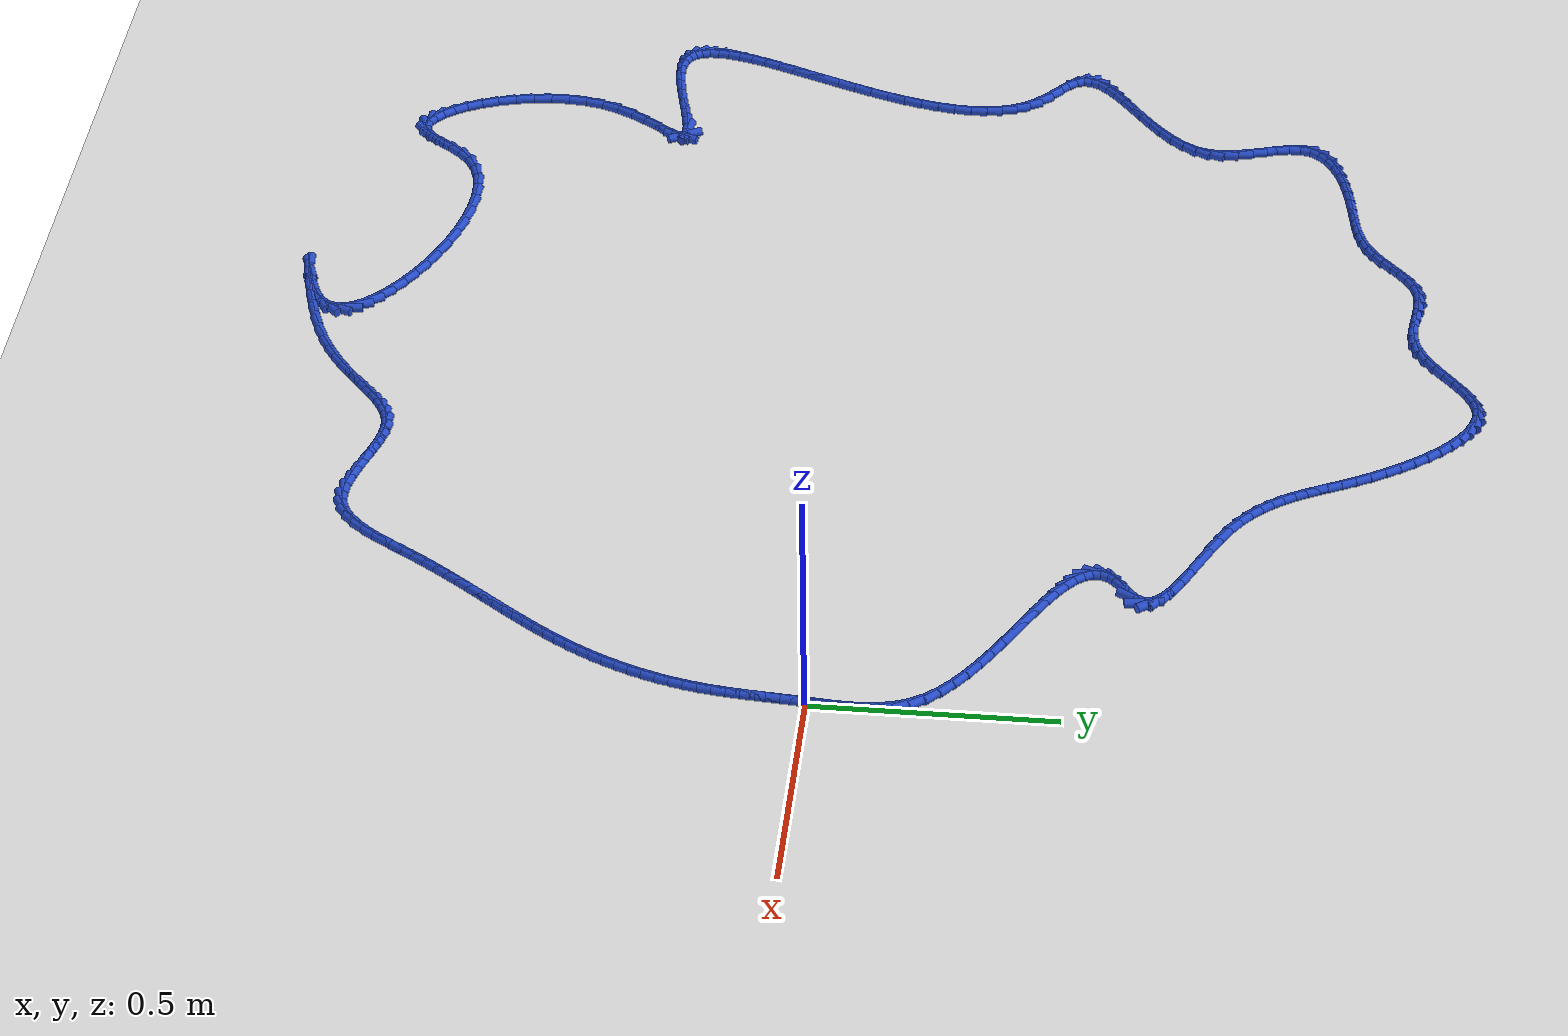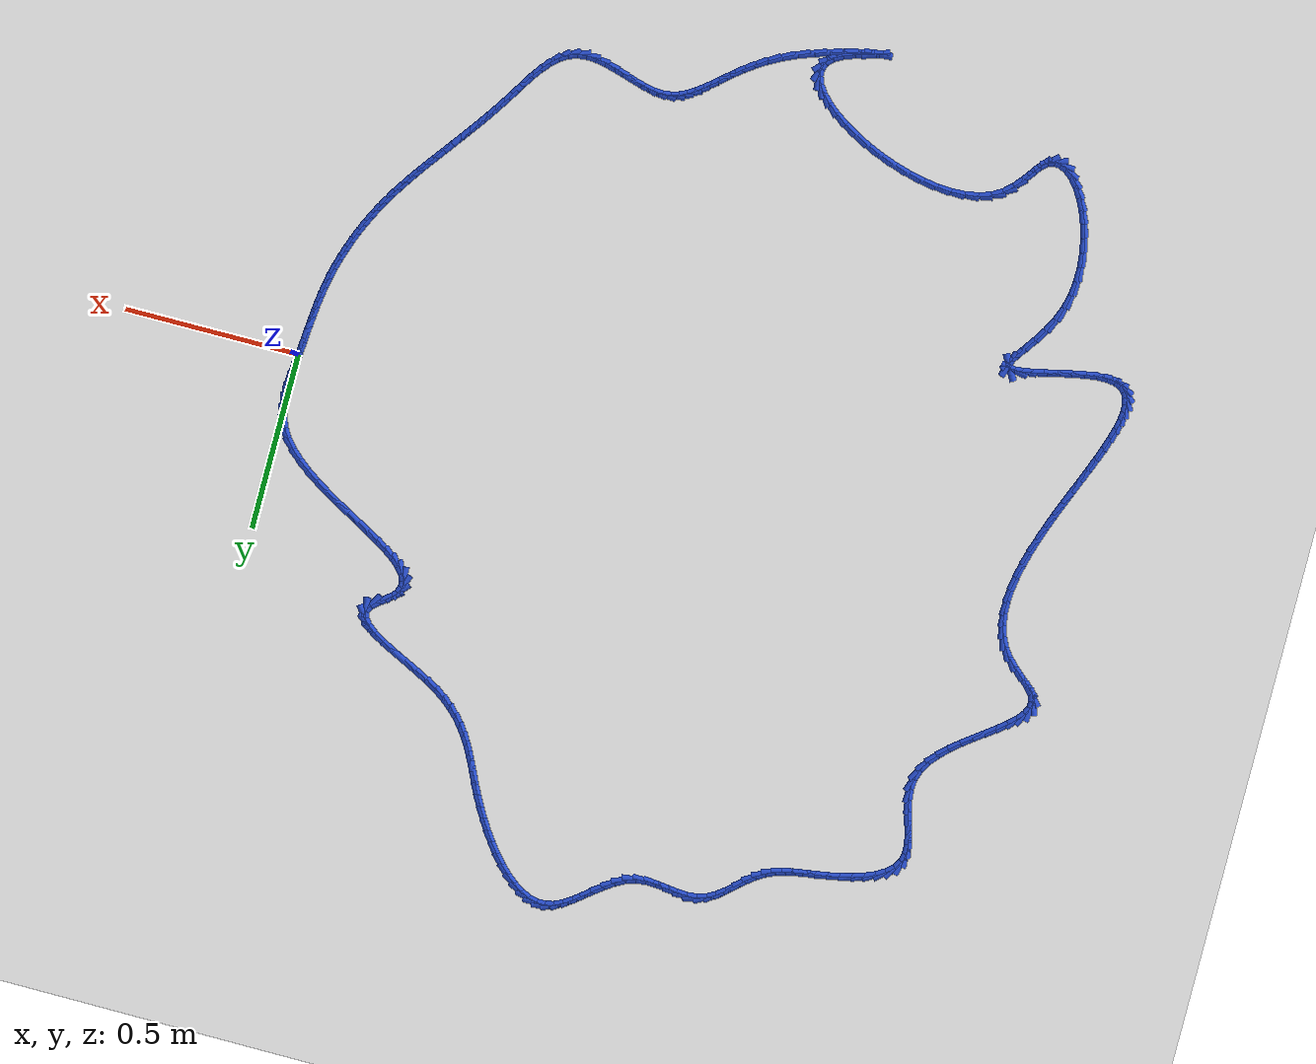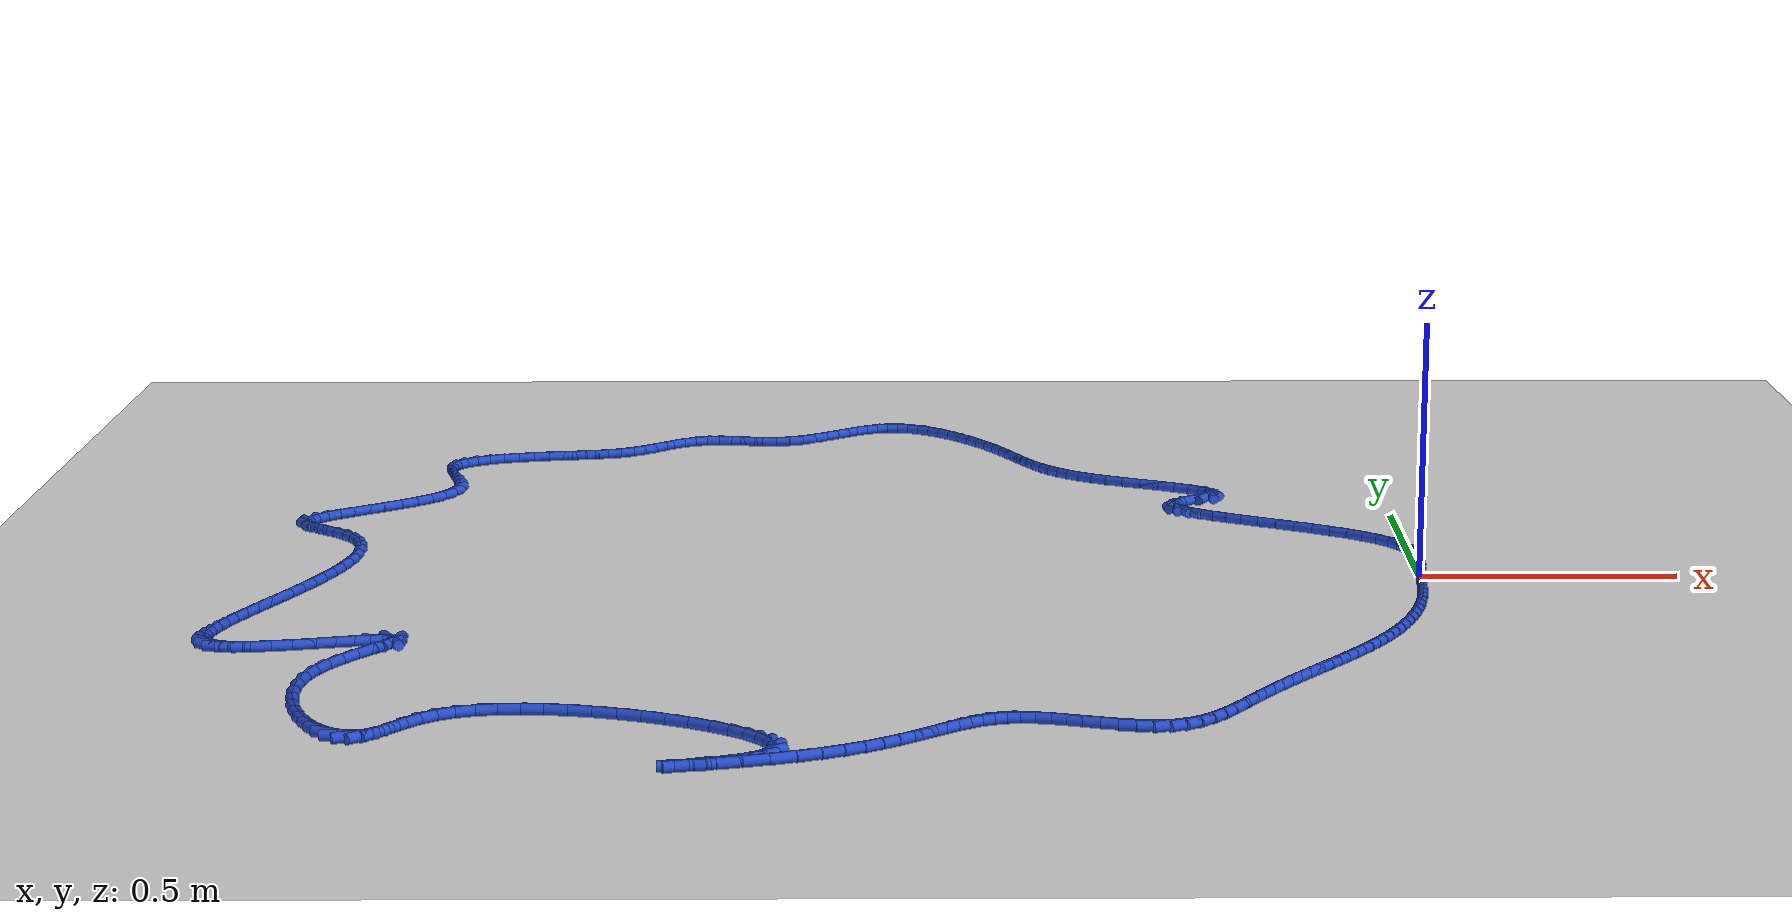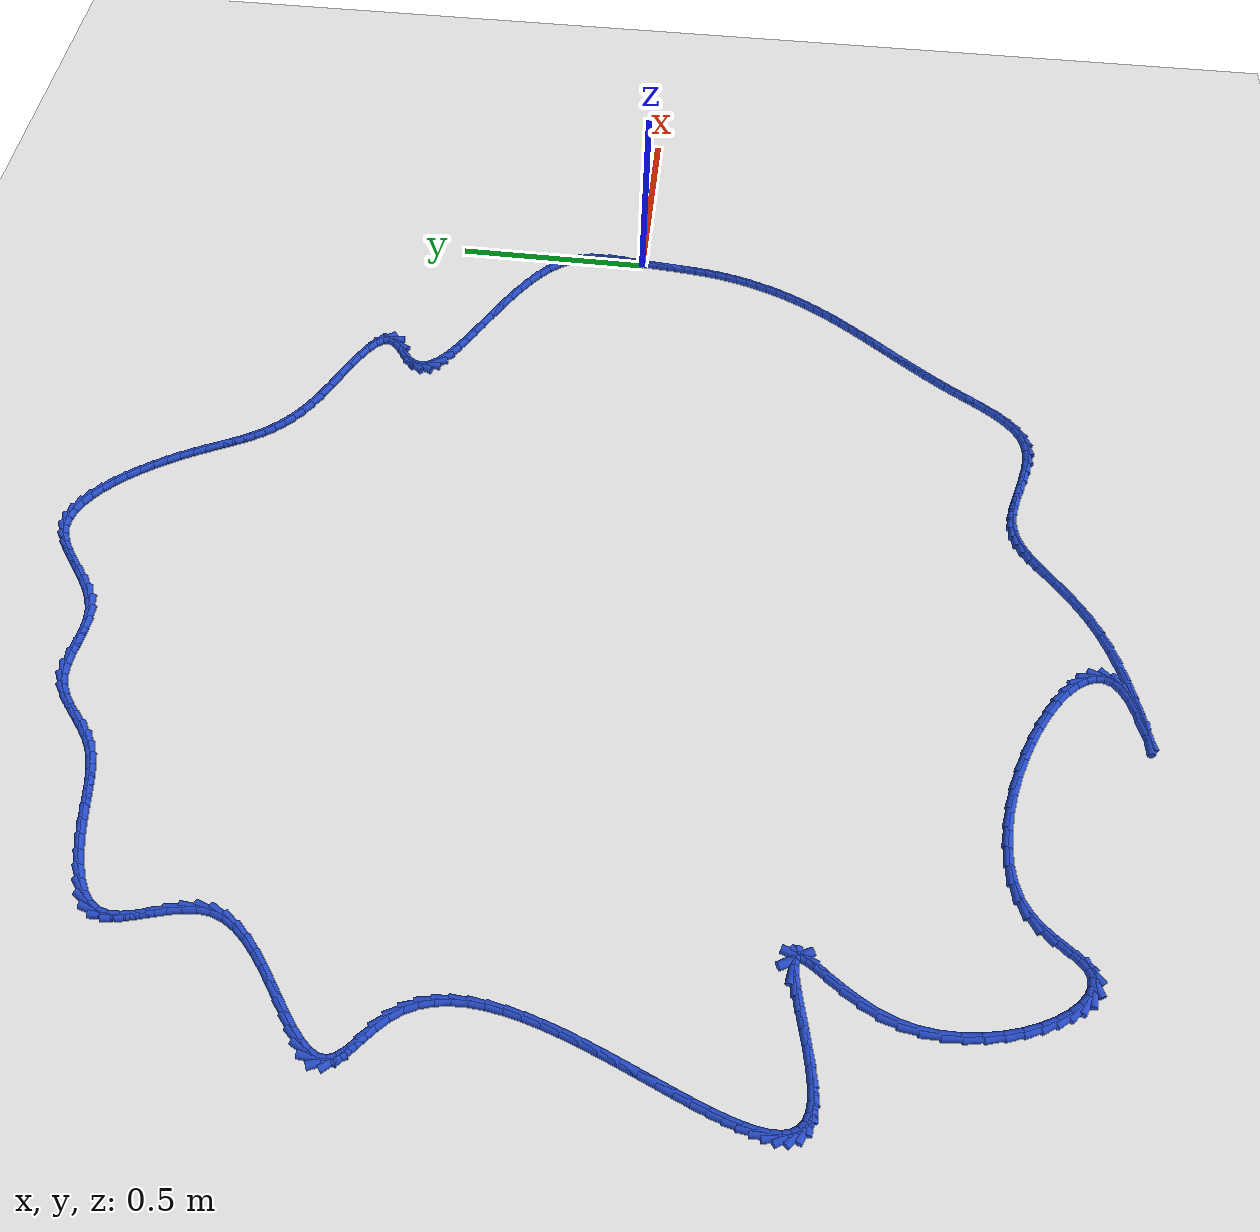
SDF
<sdf version="1.6">
 <world name="default">
  <light name="sun" type="directional">
   <pose>0 0 10 0 -0 0</pose>
   <diffuse>0.8 0.8 0.8 1</diffuse>
   <specular>0.2 0.2 0.2 1</specular>
   <attenuation>
    <range>1000</range>
    <constant>0.9</constant>
    <linear>0.01</linear>
    <quadratic>0.001</quadratic>
   </attenuation>
   <direction>-0.5 0.1 -0.9</direction>
  </light>
  <model name="ground_plane">
   <static>1</static>
   <link name="link">
    <collision name="collision">
     <geometry><plane><normal>0 0 1</normal><size>100 100</size></plane></geometry>
     <surface><friction><ode><mu>100</mu><mu2>50</mu2></ode></friction></surface>
    </collision>
    <visual name="visual">
     <cast_shadows>0</cast_shadows>
     <geometry><plane><normal>0 0 1</normal><size>100 100</size></plane></geometry>
     <material>
      <script><uri>file://media/materials/scripts/gazebo.material</uri><name>Gazebo/WhiteGlow</name></script>
     </material>
    </visual>
   </link>
  </model>
  <gravity>0 0 -9.8</gravity>
  <magnetic_field>6e-06 2.3e-05 -4.2e-05</magnetic_field>
  <atmosphere type="adiabatic"/>
  <physics name="default_physics" default="0" type="ode">
   <max_step_size>0.001</max_step_size>
   <real_time_factor>1</real_time_factor>
   <real_time_update_rate>1000</real_time_update_rate>
  </physics>
  <scene><ambient>0.4 0.4 0.4 1</ambient><background>0.7 0.7 0.7 1</background><shadows>1</shadows></scene>
  <spherical_coordinates>
   <surface_model>EARTH_WGS84</surface_model>
   <latitude_deg>0</latitude_deg>
   <longitude_deg>0</longitude_deg>
   <elevation>0</elevation>
   <heading_deg>0</heading_deg>
  </spherical_coordinates>
  <model name="line">
   <link name="link_0">
    <pose>7.806255641895632e-18 3.469446951953614e-17 0.01 0 1.57 1.4746402180226061</pose>
    <collision name="collision">
     <geometry><cylinder><radius>0.01</radius><length>0.08</length></cylinder></geometry>
    </collision>
    <visual name="visual">
     <material>
      <script><name>Gazebo/Blue</name><uri>file://media/materials/scripts/gazebo.material</uri></script>
     </material>
     <geometry><cylinder><radius>0.01</radius><length>0.08</length></cylinder></geometry>
    </visual>
   </link>
   <link name="link_1">
    <pose>0.0028988721180131347 0.030054588540749792 0.01 0 1.57 1.487445917077449</pose>
    <collision name="collision">
     <geometry><cylinder><radius>0.01</radius><length>0.08</length></cylinder></geometry>
    </collision>
    <visual name="visual">
     <material>
      <script><name>Gazebo/Blue</name><uri>file://media/materials/scripts/gazebo.material</uri></script>
     </material>
     <geometry><cylinder><radius>0.01</radius><length>0.08</length></cylinder></geometry>
    </visual>
   </link>
   <link name="link_2">
    <pose>0.005418279549983693 0.06021125345075633 0.01 0 1.57 1.5258591423656978</pose>
    <collision name="collision">
     <geometry><cylinder><radius>0.01</radius><length>0.08</length></cylinder></geometry>
    </collision>
    <visual name="visual">
     <material>
      <script><name>Gazebo/Blue</name><uri>file://media/materials/scripts/gazebo.material</uri></script>
     </material>
     <geometry><cylinder><radius>0.01</radius><length>0.08</length></cylinder></geometry>
    </visual>
   </link>
   <link name="link_3">
    <pose>0.006769807629131971 0.09026694646953276 0.01 0 1.57 -1.5504720018740654</pose>
    <collision name="collision">
     <geometry><cylinder><radius>0.01</radius><length>0.08</length></cylinder></geometry>
    </collision>
    <visual name="visual">
     <material>
      <script><name>Gazebo/Blue</name><uri>file://media/materials/scripts/gazebo.material</uri></script>
     </material>
     <geometry><cylinder><radius>0.01</radius><length>0.08</length></cylinder></geometry>
    </visual>
   </link>
   <link name="link_4">
    <pose>0.006165041688678258 0.1200186193365923 0.01 0 1.57 -1.4567601498223957</pose>
    <collision name="collision">
     <geometry><cylinder><radius>0.01</radius><length>0.08</length></cylinder></geometry>
    </collision>
    <visual name="visual">
     <material>
      <script><name>Gazebo/Blue</name><uri>file://media/materials/scripts/gazebo.material</uri></script>
     </material>
     <geometry><cylinder><radius>0.01</radius><length>0.08</length></cylinder></geometry>
    </visual>
   </link>
   <link name="link_5">
    <pose>0.0028155670618428396 0.14926322379144807 0.01 0 1.57 -1.3341143771628512</pose>
    <collision name="collision">
     <geometry><cylinder><radius>0.01</radius><length>0.08</length></cylinder></geometry>
    </collision>
    <visual name="visual">
     <material>
      <script><name>Gazebo/Blue</name><uri>file://media/materials/scripts/gazebo.material</uri></script>
     </material>
     <geometry><cylinder><radius>0.01</radius><length>0.08</length></cylinder></geometry>
    </visual>
   </link>
   <link name="link_6">
    <pose>-0.0040670309181539965 0.1777977115736131 0.01 0 1.57 -1.1854428714655687</pose>
    <collision name="collision">
     <geometry><cylinder><radius>0.01</radius><length>0.08</length></cylinder></geometry>
    </collision>
    <visual name="visual">
     <material>
      <script><name>Gazebo/Blue</name><uri>file://media/materials/scripts/gazebo.material</uri></script>
     </material>
     <geometry><cylinder><radius>0.01</radius><length>0.08</length></cylinder></geometry>
    </visual>
   </link>
   <link name="link_7">
    <pose>-0.015271166918091945 0.20541903442260076 0.01 0 1.57 -1.019436579250831</pose>
    <collision name="collision">
     <geometry><cylinder><radius>0.01</radius><length>0.08</length></cylinder></geometry>
    </collision>
    <visual name="visual">
     <material>
      <script><name>Gazebo/Blue</name><uri>file://media/materials/scripts/gazebo.material</uri></script>
     </material>
     <geometry><cylinder><radius>0.01</radius><length>0.08</length></cylinder></geometry>
    </visual>
   </link>
   <link name="link_8">
    <pose>-0.03157261234150013 0.23192641308962025 0.01 0 1.57 -0.8655247426187502</pose>
    <collision name="collision">
     <geometry><cylinder><radius>0.01</radius><length>0.08</length></cylinder></geometry>
    </collision>
    <visual name="visual">
     <material>
      <script><name>Gazebo/Blue</name><uri>file://media/materials/scripts/gazebo.material</uri></script>
     </material>
     <geometry><cylinder><radius>0.01</radius><length>0.08</length></cylinder></geometry>
    </visual>
   </link>
   <link name="link_9">
    <pose>-0.053116485852896356 0.2572322478439181 0.01 0 1.57 -0.7487405426597362</pose>
    <collision name="collision">
     <geometry><cylinder><radius>0.01</radius><length>0.08</length></cylinder></geometry>
    </collision>
    <visual name="visual">
     <material>
      <script><name>Gazebo/Blue</name><uri>file://media/materials/scripts/gazebo.material</uri></script>
     </material>
     <geometry><cylinder><radius>0.01</radius><length>0.08</length></cylinder></geometry>
    </visual>
   </link>
   <link name="link_10">
    <pose>-0.07913762132125632 0.2814123023845066 0.01 0 1.57 -0.6625558946643706</pose>
    <collision name="collision">
     <geometry><cylinder><radius>0.01</radius><length>0.08</length></cylinder></geometry>
    </collision>
    <visual name="visual">
     <material>
      <script><name>Gazebo/Blue</name><uri>file://media/materials/scripts/gazebo.material</uri></script>
     </material>
     <geometry><cylinder><radius>0.01</radius><length>0.08</length></cylinder></geometry>
    </visual>
   </link>
   <link name="link_11">
    <pose>-0.10879991081243584 0.30455507191632625 0.01 0 1.57 -0.5996197437714119</pose>
    <collision name="collision">
     <geometry><cylinder><radius>0.01</radius><length>0.08</length></cylinder></geometry>
    </collision>
    <visual name="visual">
     <material>
      <script><name>Gazebo/Blue</name><uri>file://media/materials/scripts/gazebo.material</uri></script>
     </material>
     <geometry><cylinder><radius>0.01</radius><length>0.08</length></cylinder></geometry>
    </visual>
   </link>
   <link name="link_12">
    <pose>-0.14126724639229082 0.32674905164431783 0.01 0 1.57 -0.5546431576381627</pose>
    <collision name="collision">
     <geometry><cylinder><radius>0.01</radius><length>0.08</length></cylinder></geometry>
    </collision>
    <visual name="visual">
     <material>
      <script><name>Gazebo/Blue</name><uri>file://media/materials/scripts/gazebo.material</uri></script>
     </material>
     <geometry><cylinder><radius>0.01</radius><length>0.08</length></cylinder></geometry>
    </visual>
   </link>
   <link name="link_13">
    <pose>-0.17570352012667736 0.3480827367734225 0.01 0 1.57 -0.524147968410505</pose>
    <collision name="collision">
     <geometry><cylinder><radius>0.01</radius><length>0.08</length></cylinder></geometry>
    </collision>
    <visual name="visual">
     <material>
      <script><name>Gazebo/Blue</name><uri>file://media/materials/scripts/gazebo.material</uri></script>
     </material>
     <geometry><cylinder><radius>0.01</radius><length>0.08</length></cylinder></geometry>
    </visual>
   </link>
   <link name="link_14">
    <pose>-0.21127262408145103 0.3686446225085807 0.01 0 1.57 -0.5060991870181922</pose>
    <collision name="collision">
     <geometry><cylinder><radius>0.01</radius><length>0.08</length></cylinder></geometry>
    </collision>
    <visual name="visual">
     <material>
      <script><name>Gazebo/Blue</name><uri>file://media/materials/scripts/gazebo.material</uri></script>
     </material>
     <geometry><cylinder><radius>0.01</radius><length>0.08</length></cylinder></geometry>
    </visual>
   </link>
   <link name="link_15">
    <pose>-0.24713845032246806 0.3885232040547336 0.01 0 1.57 -0.4996696578759354</pose>
    <collision name="collision">
     <geometry><cylinder><radius>0.01</radius><length>0.08</length></cylinder></geometry>
    </collision>
    <visual name="visual">
     <material>
      <script><name>Gazebo/Blue</name><uri>file://media/materials/scripts/gazebo.material</uri></script>
     </material>
     <geometry><cylinder><radius>0.01</radius><length>0.08</length></cylinder></geometry>
    </visual>
   </link>
   <link name="link_16">
    <pose>-0.2824648909155843 0.40780697661682197 0.01 0 1.57 -0.5052018639270373</pose>
    <collision name="collision">
     <geometry><cylinder><radius>0.01</radius><length>0.08</length></cylinder></geometry>
    </collision>
    <visual name="visual">
     <material>
      <script><name>Gazebo/Blue</name><uri>file://media/materials/scripts/gazebo.material</uri></script>
     </material>
     <geometry><cylinder><radius>0.01</radius><length>0.08</length></cylinder></geometry>
    </visual>
   </link>
   <link name="link_17">
    <pose>-0.3164158379266554 0.42658443539978635 0.01 0 1.57 -0.5244235541090694</pose>
    <collision name="collision">
     <geometry><cylinder><radius>0.01</radius><length>0.08</length></cylinder></geometry>
    </collision>
    <visual name="visual">
     <material>
      <script><name>Gazebo/Blue</name><uri>file://media/materials/scripts/gazebo.material</uri></script>
     </material>
     <geometry><cylinder><radius>0.01</radius><length>0.08</length></cylinder></geometry>
    </visual>
   </link>
   <link name="link_18">
    <pose>-0.3481551834215377 0.4449440756085682 0.01 0 1.57 -0.5610528359125257</pose>
    <collision name="collision">
     <geometry><cylinder><radius>0.01</radius><length>0.08</length></cylinder></geometry>
    </collision>
    <visual name="visual">
     <material>
      <script><name>Gazebo/Blue</name><uri>file://media/materials/scripts/gazebo.material</uri></script>
     </material>
     <geometry><cylinder><radius>0.01</radius><length>0.08</length></cylinder></geometry>
    </visual>
   </link>
   <link name="link_19">
    <pose>-0.37684681946608684 0.46297439244810773 0.01 0 1.57 -0.6221052469594506</pose>
    <collision name="collision">
     <geometry><cylinder><radius>0.01</radius><length>0.08</length></cylinder></geometry>
    </collision>
    <visual name="visual">
     <material>
      <script><name>Gazebo/Blue</name><uri>file://media/materials/scripts/gazebo.material</uri></script>
     </material>
     <geometry><cylinder><radius>0.01</radius><length>0.08</length></cylinder></geometry>
    </visual>
   </link>
   <link name="link_20">
    <pose>-0.40165463812615865 0.48076388112334595 0.01 0 1.57 -0.7205261791843238</pose>
    <collision name="collision">
     <geometry><cylinder><radius>0.01</radius><length>0.08</length></cylinder></geometry>
    </collision>
    <visual name="visual">
     <material>
      <script><name>Gazebo/Blue</name><uri>file://media/materials/scripts/gazebo.material</uri></script>
     </material>
     <geometry><cylinder><radius>0.01</radius><length>0.08</length></cylinder></geometry>
    </visual>
   </link>
   <link name="link_21">
    <pose>-0.4217425314676093 0.4984010368392238 0.01 0 1.57 -0.8798504651959707</pose>
    <collision name="collision">
     <geometry><cylinder><radius>0.01</radius><length>0.08</length></cylinder></geometry>
    </collision>
    <visual name="visual">
     <material>
      <script><name>Gazebo/Blue</name><uri>file://media/materials/scripts/gazebo.material</uri></script>
     </material>
     <geometry><cylinder><radius>0.01</radius><length>0.08</length></cylinder></geometry>
    </visual>
   </link>
   <link name="link_22">
    <pose>-0.43627439155629455 0.515974354800682 0.01 0 1.57 -1.137565484481062</pose>
    <collision name="collision">
     <geometry><cylinder><radius>0.01</radius><length>0.08</length></cylinder></geometry>
    </collision>
    <visual name="visual">
     <material>
      <script><name>Gazebo/Blue</name><uri>file://media/materials/scripts/gazebo.material</uri></script>
     </material>
     <geometry><cylinder><radius>0.01</radius><length>0.08</length></cylinder></geometry>
    </visual>
   </link>
   <link name="link_23">
    <pose>-0.4444141104580702 0.5335723302126616 0.01 0 1.57 -1.519378574509934</pose>
    <collision name="collision">
     <geometry><cylinder><radius>0.01</radius><length>0.08</length></cylinder></geometry>
    </collision>
    <visual name="visual">
     <material>
      <script><name>Gazebo/Blue</name><uri>file://media/materials/scripts/gazebo.material</uri></script>
     </material>
     <geometry><cylinder><radius>0.01</radius><length>0.08</length></cylinder></geometry>
    </visual>
   </link>
   <link name="link_24">
    <pose>-0.44532558023879243 0.5512834582801032 0.01 0 1.57 1.1908783359319826</pose>
    <collision name="collision">
     <geometry><cylinder><radius>0.01</radius><length>0.08</length></cylinder></geometry>
    </collision>
    <visual name="visual">
     <material>
      <script><name>Gazebo/Blue</name><uri>file://media/materials/scripts/gazebo.material</uri></script>
     </material>
     <geometry><cylinder><radius>0.01</radius><length>0.08</length></cylinder></geometry>
    </visual>
   </link>
   <link name="link_25">
    <pose>-0.43817269296431705 0.5691962342079477 0.01 0 1.57 0.8480655811776272</pose>
    <collision name="collision">
     <geometry><cylinder><radius>0.01</radius><length>0.08</length></cylinder></geometry>
    </collision>
    <visual name="visual">
     <material>
      <script><name>Gazebo/Blue</name><uri>file://media/materials/scripts/gazebo.material</uri></script>
     </material>
     <geometry><cylinder><radius>0.01</radius><length>0.08</length></cylinder></geometry>
    </visual>
   </link>
   <link name="link_26">
    <pose>-0.4221193407004997 0.5873991532011358 0.01 0 1.57 0.6605520184258402</pose>
    <collision name="collision">
     <geometry><cylinder><radius>0.01</radius><length>0.08</length></cylinder></geometry>
    </collision>
    <visual name="visual">
     <material>
      <script><name>Gazebo/Blue</name><uri>file://media/materials/scripts/gazebo.material</uri></script>
     </material>
     <geometry><cylinder><radius>0.01</radius><length>0.08</length></cylinder></geometry>
    </visual>
   </link>
   <link name="link_27">
    <pose>-0.39830640936015027 0.6059015582609163 0.01 0 1.57 0.7055435479070159</pose>
    <collision name="collision">
     <geometry><cylinder><radius>0.01</radius><length>0.08</length></cylinder></geometry>
    </collision>
    <visual name="visual">
     <material>
      <script><name>Gazebo/Blue</name><uri>file://media/materials/scripts/gazebo.material</uri></script>
     </material>
     <geometry><cylinder><radius>0.01</radius><length>0.08</length></cylinder></geometry>
    </visual>
   </link>
   <link name="link_28">
    <pose>-0.37663426658869226 0.6243620921152869 0.01 0 1.57 1.0853191289259294</pose>
    <collision name="collision">
     <geometry><cylinder><radius>0.01</radius><length>0.08</length></cylinder></geometry>
    </collision>
    <visual name="visual">
     <material>
      <script><name>Gazebo/Blue</name><uri>file://media/materials/scripts/gazebo.material</uri></script>
     </material>
     <geometry><cylinder><radius>0.01</radius><length>0.08</length></cylinder></geometry>
    </visual>
   </link>
   <link name="link_29">
    <pose>-0.3671003697334355 0.6424326602242847 0.01 0 1.57 -1.399066620463761</pose>
    <collision name="collision">
     <geometry><cylinder><radius>0.01</radius><length>0.08</length></cylinder></geometry>
    </collision>
    <visual name="visual">
     <material>
      <script><name>Gazebo/Blue</name><uri>file://media/materials/scripts/gazebo.material</uri></script>
     </material>
     <geometry><cylinder><radius>0.01</radius><length>0.08</length></cylinder></geometry>
    </visual>
   </link>
   <link name="link_30">
    <pose>-0.37017064761934426 0.6601351095823516 0.01 0 1.57 -0.9051813185605434</pose>
    <collision name="collision">
     <geometry><cylinder><radius>0.01</radius><length>0.08</length></cylinder></geometry>
    </collision>
    <visual name="visual">
     <material>
      <script><name>Gazebo/Blue</name><uri>file://media/materials/scripts/gazebo.material</uri></script>
     </material>
     <geometry><cylinder><radius>0.01</radius><length>0.08</length></cylinder></geometry>
    </visual>
   </link>
   <link name="link_31">
    <pose>-0.383872027789305 0.6775859507138687 0.01 0 1.57 -0.6589523620478688</pose>
    <collision name="collision">
     <geometry><cylinder><radius>0.01</radius><length>0.08</length></cylinder></geometry>
    </collision>
    <visual name="visual">
     <material>
      <script><name>Gazebo/Blue</name><uri>file://media/materials/scripts/gazebo.material</uri></script>
     </material>
     <geometry><cylinder><radius>0.01</radius><length>0.08</length></cylinder></geometry>
    </visual>
   </link>
   <link name="link_32">
    <pose>-0.4062314366739607 0.6949016941863856 0.01 0 1.57 -0.5371355620843321</pose>
    <collision name="collision">
     <geometry><cylinder><radius>0.01</radius><length>0.08</length></cylinder></geometry>
    </collision>
    <visual name="visual">
     <material>
      <script><name>Gazebo/Blue</name><uri>file://media/materials/scripts/gazebo.material</uri></script>
     </material>
     <geometry><cylinder><radius>0.01</radius><length>0.08</length></cylinder></geometry>
    </visual>
   </link>
   <link name="link_33">
    <pose>-0.43527580070395433 0.7121988505674522 0.01 0 1.57 -0.4758239437813199</pose>
    <collision name="collision">
     <geometry><cylinder><radius>0.01</radius><length>0.08</length></cylinder></geometry>
    </collision>
    <visual name="visual">
     <material>
      <script><name>Gazebo/Blue</name><uri>file://media/materials/scripts/gazebo.material</uri></script>
     </material>
     <geometry><cylinder><radius>0.01</radius><length>0.08</length></cylinder></geometry>
    </visual>
   </link>
   <link name="link_34">
    <pose>-0.4690320463099283 0.7295939304246174 0.01 0 1.57 -0.44956431116818246</pose>
    <collision name="collision">
     <geometry><cylinder><radius>0.01</radius><length>0.08</length></cylinder></geometry>
    </collision>
    <visual name="visual">
     <material>
      <script><name>Gazebo/Blue</name><uri>file://media/materials/scripts/gazebo.material</uri></script>
     </material>
     <geometry><cylinder><radius>0.01</radius><length>0.08</length></cylinder></geometry>
    </visual>
   </link>
   <link name="link_35">
    <pose>-0.505527099922526 0.747203444325432 0.01 0 1.57 -0.44872506694509867</pose>
    <collision name="collision">
     <geometry><cylinder><radius>0.01</radius><length>0.08</length></cylinder></geometry>
    </collision>
    <visual name="visual">
     <material>
      <script><name>Gazebo/Blue</name><uri>file://media/materials/scripts/gazebo.material</uri></script>
     </material>
     <geometry><cylinder><radius>0.01</radius><length>0.08</length></cylinder></geometry>
    </visual>
   </link>
   <link name="link_36">
    <pose>-0.5427878879723895 0.765143902837445 0.01 0 1.57 -0.4716299795766024</pose>
    <collision name="collision">
     <geometry><cylinder><radius>0.01</radius><length>0.08</length></cylinder></geometry>
    </collision>
    <visual name="visual">
     <material>
      <script><name>Gazebo/Blue</name><uri>file://media/materials/scripts/gazebo.material</uri></script>
     </material>
     <geometry><cylinder><radius>0.01</radius><length>0.08</length></cylinder></geometry>
    </visual>
   </link>
   <link name="link_37">
    <pose>-0.5788413368901628 0.7835318165282066 0.01 0 1.57 -0.5228354173593845</pose>
    <collision name="collision">
     <geometry><cylinder><radius>0.01</radius><length>0.08</length></cylinder></geometry>
    </collision>
    <visual name="visual">
     <material>
      <script><name>Gazebo/Blue</name><uri>file://media/materials/scripts/gazebo.material</uri></script>
     </material>
     <geometry><cylinder><radius>0.01</radius><length>0.08</length></cylinder></geometry>
    </visual>
   </link>
   <link name="link_38">
    <pose>-0.6117242793091663 0.802483338303012 0.01 0 1.57 -0.6007688888644219</pose>
    <collision name="collision">
     <geometry><cylinder><radius>0.01</radius><length>0.08</length></cylinder></geometry>
    </collision>
    <visual name="visual">
     <material>
      <script><name>Gazebo/Blue</name><uri>file://media/materials/scripts/gazebo.material</uri></script>
     </material>
     <geometry><cylinder><radius>0.01</radius><length>0.08</length></cylinder></geometry>
    </visual>
   </link>
   <link name="link_39">
    <pose>-0.640326989284692 0.8220838076674509 0.01 0 1.57 -0.6872440952796394</pose>
    <collision name="collision">
     <geometry><cylinder><radius>0.01</radius><length>0.08</length></cylinder></geometry>
    </collision>
    <visual name="visual">
     <material>
      <script><name>Gazebo/Blue</name><uri>file://media/materials/scripts/gazebo.material</uri></script>
     </material>
     <geometry><cylinder><radius>0.01</radius><length>0.08</length></cylinder></geometry>
    </visual>
   </link>
   <link name="link_40">
    <pose>-0.6650380040360955 0.8423644695161051 0.01 0 1.57 -0.7765887038904971</pose>
    <collision name="collision">
     <geometry><cylinder><radius>0.01</radius><length>0.08</length></cylinder></geometry>
    </collision>
    <visual name="visual">
     <material>
      <script><name>Gazebo/Blue</name><uri>file://media/materials/scripts/gazebo.material</uri></script>
     </material>
     <geometry><cylinder><radius>0.01</radius><length>0.08</length></cylinder></geometry>
    </visual>
   </link>
   <link name="link_41">
    <pose>-0.6863976794744341 0.8633510873479857 0.01 0 1.57 -0.8639518343235093</pose>
    <collision name="collision">
     <geometry><cylinder><radius>0.01</radius><length>0.08</length></cylinder></geometry>
    </collision>
    <visual name="visual">
     <material>
      <script><name>Gazebo/Blue</name><uri>file://media/materials/scripts/gazebo.material</uri></script>
     </material>
     <geometry><cylinder><radius>0.01</radius><length>0.08</length></cylinder></geometry>
    </visual>
   </link>
   <link name="link_42">
    <pose>-0.7049463715107641 0.8850694246621034 0.01 0 1.57 -0.9439813212533213</pose>
    <collision name="collision">
     <geometry><cylinder><radius>0.01</radius><length>0.08</length></cylinder></geometry>
    </collision>
    <visual name="visual">
     <material>
      <script><name>Gazebo/Blue</name><uri>file://media/materials/scripts/gazebo.material</uri></script>
     </material>
     <geometry><cylinder><radius>0.01</radius><length>0.08</length></cylinder></geometry>
    </visual>
   </link>
   <link name="link_43">
    <pose>-0.7212244360561426 0.9075452449574696 0.01 0 1.57 -1.0118608214335638</pose>
    <collision name="collision">
     <geometry><cylinder><radius>0.01</radius><length>0.08</length></cylinder></geometry>
    </collision>
    <visual name="visual">
     <material>
      <script><name>Gazebo/Blue</name><uri>file://media/materials/scripts/gazebo.material</uri></script>
     </material>
     <geometry><cylinder><radius>0.01</radius><length>0.08</length></cylinder></geometry>
    </visual>
   </link>
   <link name="link_44">
    <pose>-0.7357722290216261 0.9308043117330957 0.01 0 1.57 -1.0641194428040195</pose>
    <collision name="collision">
     <geometry><cylinder><radius>0.01</radius><length>0.08</length></cylinder></geometry>
    </collision>
    <visual name="visual">
     <material>
      <script><name>Gazebo/Blue</name><uri>file://media/materials/scripts/gazebo.material</uri></script>
     </material>
     <geometry><cylinder><radius>0.01</radius><length>0.08</length></cylinder></geometry>
    </visual>
   </link>
   <link name="link_45">
    <pose>-0.749130106318271 0.9548723884879919 0.01 0 1.57 -1.0989301886839935</pose>
    <collision name="collision">
     <geometry><cylinder><radius>0.01</radius><length>0.08</length></cylinder></geometry>
    </collision>
    <visual name="visual">
     <material>
      <script><name>Gazebo/Blue</name><uri>file://media/materials/scripts/gazebo.material</uri></script>
     </material>
     <geometry><cylinder><radius>0.01</radius><length>0.08</length></cylinder></geometry>
    </visual>
   </link>
   <link name="link_46">
    <pose>-0.761838423857135 0.9797752387211703 0.01 0 1.57 -1.1159617761510223</pose>
    <collision name="collision">
     <geometry><cylinder><radius>0.01</radius><length>0.08</length></cylinder></geometry>
    </collision>
    <visual name="visual">
     <material>
      <script><name>Gazebo/Blue</name><uri>file://media/materials/scripts/gazebo.material</uri></script>
     </material>
     <geometry><cylinder><radius>0.01</radius><length>0.08</length></cylinder></geometry>
    </visual>
   </link>
   <link name="link_47">
    <pose>-0.7744375375492735 1.0055386259316412 0.01 0 1.57 -1.11603072998117</pose>
    <collision name="collision">
     <geometry><cylinder><radius>0.01</radius><length>0.08</length></cylinder></geometry>
    </collision>
    <visual name="visual">
     <material>
      <script><name>Gazebo/Blue</name><uri>file://media/materials/scripts/gazebo.material</uri></script>
     </material>
     <geometry><cylinder><radius>0.01</radius><length>0.08</length></cylinder></geometry>
    </visual>
   </link>
   <link name="link_48">
    <pose>-0.7874678033057438 1.032188313618416 0.01 0 1.57 -1.1007575710946635</pose>
    <collision name="collision">
     <geometry><cylinder><radius>0.01</radius><length>0.08</length></cylinder></geometry>
    </collision>
    <visual name="visual">
     <material>
      <script><name>Gazebo/Blue</name><uri>file://media/materials/scripts/gazebo.material</uri></script>
     </material>
     <geometry><cylinder><radius>0.01</radius><length>0.08</length></cylinder></geometry>
    </visual>
   </link>
   <link name="link_49">
    <pose>-0.8014695770376029 1.0597500652805056 0.01 0 1.57 -1.072435974765913</pose>
    <collision name="collision">
     <geometry><cylinder><radius>0.01</radius><length>0.08</length></cylinder></geometry>
    </collision>
    <visual name="visual">
     <material>
      <script><name>Gazebo/Blue</name><uri>file://media/materials/scripts/gazebo.material</uri></script>
     </material>
     <geometry><cylinder><radius>0.01</radius><length>0.08</length></cylinder></geometry>
    </visual>
   </link>
   <link name="link_50">
    <pose>-0.8169733712081978 1.088240500938961 0.01 0 1.57 -1.037093741614233</pose>
    <collision name="collision">
     <geometry><cylinder><radius>0.01</radius><length>0.08</length></cylinder></geometry>
    </collision>
    <visual name="visual">
     <material>
      <script><name>Gazebo/Blue</name><uri>file://media/materials/scripts/gazebo.material</uri></script>
     </material>
     <geometry><cylinder><radius>0.01</radius><length>0.08</length></cylinder></geometry>
    </visual>
   </link>
   <link name="link_51">
    <pose>-0.8341933649110843 1.1173824017810994 0.01 0 1.57 -0.9988732437890054</pose>
    <collision name="collision">
     <geometry><cylinder><radius>0.01</radius><length>0.08</length></cylinder></geometry>
    </collision>
    <visual name="visual">
     <material>
      <script><name>Gazebo/Blue</name><uri>file://media/materials/scripts/gazebo.material</uri></script>
     </material>
     <geometry><cylinder><radius>0.01</radius><length>0.08</length></cylinder></geometry>
    </visual>
   </link>
   <link name="link_52">
    <pose>-0.8529675277920749 1.146549091883731 0.01 0 1.57 -0.9562418841616519</pose>
    <collision name="collision">
     <geometry><cylinder><radius>0.01</radius><length>0.08</length></cylinder></geometry>
    </collision>
    <visual name="visual">
     <material>
      <script><name>Gazebo/Blue</name><uri>file://media/materials/scripts/gazebo.material</uri></script>
     </material>
     <geometry><cylinder><radius>0.01</radius><length>0.08</length></cylinder></geometry>
    </visual>
   </link>
   <link name="link_53">
    <pose>-0.8731118979140977 1.1750935233005042 0.01 0 1.57 -0.9070943729636897</pose>
    <collision name="collision">
     <geometry><cylinder><radius>0.01</radius><length>0.08</length></cylinder></geometry>
    </collision>
    <visual name="visual">
     <material>
      <script><name>Gazebo/Blue</name><uri>file://media/materials/scripts/gazebo.material</uri></script>
     </material>
     <geometry><cylinder><radius>0.01</radius><length>0.08</length></cylinder></geometry>
    </visual>
   </link>
   <link name="link_54">
    <pose>-0.8944425133400808 1.2023686480850653 0.01 0 1.57 -0.8487597751125688</pose>
    <collision name="collision">
     <geometry><cylinder><radius>0.01</radius><length>0.08</length></cylinder></geometry>
    </collision>
    <visual name="visual">
     <material>
      <script><name>Gazebo/Blue</name><uri>file://media/materials/scripts/gazebo.material</uri></script>
     </material>
     <geometry><cylinder><radius>0.01</radius><length>0.08</length></cylinder></geometry>
    </visual>
   </link>
   <link name="link_55">
    <pose>-0.9167754121329532 1.2277274182910622 0.01 0 1.57 -0.7776534005548527</pose>
    <collision name="collision">
     <geometry><cylinder><radius>0.01</radius><length>0.08</length></cylinder></geometry>
    </collision>
    <visual name="visual">
     <material>
      <script><name>Gazebo/Blue</name><uri>file://media/materials/scripts/gazebo.material</uri></script>
     </material>
     <geometry><cylinder><radius>0.01</radius><length>0.08</length></cylinder></geometry>
    </visual>
   </link>
   <link name="link_56">
    <pose>-0.9399266323556422 1.2505227859721428 0.01 0 1.57 -0.6888440345847494</pose>
    <collision name="collision">
     <geometry><cylinder><radius>0.01</radius><length>0.08</length></cylinder></geometry>
    </collision>
    <visual name="visual">
     <material>
      <script><name>Gazebo/Blue</name><uri>file://media/materials/scripts/gazebo.material</uri></script>
     </material>
     <geometry><cylinder><radius>0.01</radius><length>0.08</length></cylinder></geometry>
    </visual>
   </link>
   <link name="link_57">
    <pose>-0.963712212071077 1.2701077031819545 0.01 0 1.57 -0.5756216705690352</pose>
    <collision name="collision">
     <geometry><cylinder><radius>0.01</radius><length>0.08</length></cylinder></geometry>
    </collision>
    <visual name="visual">
     <material>
      <script><name>Gazebo/Blue</name><uri>file://media/materials/scripts/gazebo.material</uri></script>
     </material>
     <geometry><cylinder><radius>0.01</radius><length>0.08</length></cylinder></geometry>
    </visual>
   </link>
   <link name="link_58">
    <pose>-0.9879481893421848 1.2858351219741437 0.01 0 1.57 -0.4295126640115256</pose>
    <collision name="collision">
     <geometry><cylinder><radius>0.01</radius><length>0.08</length></cylinder></geometry>
    </collision>
    <visual name="visual">
     <material>
      <script><name>Gazebo/Blue</name><uri>file://media/materials/scripts/gazebo.material</uri></script>
     </material>
     <geometry><cylinder><radius>0.01</radius><length>0.08</length></cylinder></geometry>
    </visual>
   </link>
   <link name="link_59">
    <pose>-1.0124506022318949 1.2970579944023592 0.01 0 1.57 -0.24210756927522742</pose>
    <collision name="collision">
     <geometry><cylinder><radius>0.01</radius><length>0.08</length></cylinder></geometry>
    </collision>
    <visual name="visual">
     <material>
      <script><name>Gazebo/Blue</name><uri>file://media/materials/scripts/gazebo.material</uri></script>
     </material>
     <geometry><cylinder><radius>0.01</radius><length>0.08</length></cylinder></geometry>
    </visual>
   </link>
   <link name="link_60">
    <pose>-1.0370354888031346 1.303129272520248 0.01 0 1.57 -0.011135079761427911</pose>
    <collision name="collision">
     <geometry><cylinder><radius>0.01</radius><length>0.08</length></cylinder></geometry>
    </collision>
    <visual name="visual">
     <material>
      <script><name>Gazebo/Blue</name><uri>file://media/materials/scripts/gazebo.material</uri></script>
     </material>
     <geometry><cylinder><radius>0.01</radius><length>0.08</length></cylinder></geometry>
    </visual>
   </link>
   <link name="link_61">
    <pose>-1.0615188871188328 1.3034019083814574 0.01 0 1.57 0.2448142291321538</pose>
    <collision name="collision">
     <geometry><cylinder><radius>0.01</radius><length>0.08</length></cylinder></geometry>
    </collision>
    <visual name="visual">
     <material>
      <script><name>Gazebo/Blue</name><uri>file://media/materials/scripts/gazebo.material</uri></script>
     </material>
     <geometry><cylinder><radius>0.01</radius><length>0.08</length></cylinder></geometry>
    </visual>
   </link>
   <link name="link_62">
    <pose>-1.0857383292443321 1.2973512790820256 0.01 0 1.57 0.45145249089502715</pose>
    <collision name="collision">
     <geometry><cylinder><radius>0.01</radius><length>0.08</length></cylinder></geometry>
    </collision>
    <visual name="visual">
     <material>
      <script><name>Gazebo/Blue</name><uri>file://media/materials/scripts/gazebo.material</uri></script>
     </material>
     <geometry><cylinder><radius>0.01</radius><length>0.08</length></cylinder></geometry>
    </visual>
   </link>
   <link name="link_63">
    <pose>-1.109751798472275 1.2857084027255032 0.01 0 1.57 0.5813513070207619</pose>
    <collision name="collision">
     <geometry><cylinder><radius>0.01</radius><length>0.08</length></cylinder></geometry>
    </collision>
    <visual name="visual">
     <material>
      <script><name>Gazebo/Blue</name><uri>file://media/materials/scripts/gazebo.material</uri></script>
     </material>
     <geometry><cylinder><radius>0.01</radius><length>0.08</length></cylinder></geometry>
    </visual>
   </link>
   <link name="link_64">
    <pose>-1.133746678114327 1.269941331054357 0.01 0 1.57 0.6511332675026256</pose>
    <collision name="collision">
     <geometry><cylinder><radius>0.01</radius><length>0.08</length></cylinder></geometry>
    </collision>
    <visual name="visual">
     <material>
      <script><name>Gazebo/Blue</name><uri>file://media/materials/scripts/gazebo.material</uri></script>
     </material>
     <geometry><cylinder><radius>0.01</radius><length>0.08</length></cylinder></geometry>
    </visual>
   </link>
   <link name="link_65">
    <pose>-1.157911998771127 1.2515274984015263 0.01 0 1.57 0.6738284440458515</pose>
    <collision name="collision">
     <geometry><cylinder><radius>0.01</radius><length>0.08</length></cylinder></geometry>
    </collision>
    <visual name="visual">
     <material>
      <script><name>Gazebo/Blue</name><uri>file://media/materials/scripts/gazebo.material</uri></script>
     </material>
     <geometry><cylinder><radius>0.01</radius><length>0.08</length></cylinder></geometry>
    </visual>
   </link>
   <link name="link_66">
    <pose>-1.1824367910433156 1.2319443390999525 0.01 0 1.57 0.6553924204629619</pose>
    <collision name="collision">
     <geometry><cylinder><radius>0.01</radius><length>0.08</length></cylinder></geometry>
    </collision>
    <visual name="visual">
     <material>
      <script><name>Gazebo/Blue</name><uri>file://media/materials/scripts/gazebo.material</uri></script>
     </material>
     <geometry><cylinder><radius>0.01</radius><length>0.08</length></cylinder></geometry>
    </visual>
   </link>
   <link name="link_67">
    <pose>-1.2075100855315306 1.212669287482575 0.01 0 1.57 0.5955361580434043</pose>
    <collision name="collision">
     <geometry><cylinder><radius>0.01</radius><length>0.08</length></cylinder></geometry>
    </collision>
    <visual name="visual">
     <material>
      <script><name>Gazebo/Blue</name><uri>file://media/materials/scripts/gazebo.material</uri></script>
     </material>
     <geometry><cylinder><radius>0.01</radius><length>0.08</length></cylinder></geometry>
    </visual>
   </link>
   <link name="link_68">
    <pose>-1.233320912836411 1.1951797778823343 0.01 0 1.57 0.4889840245981175</pose>
    <collision name="collision">
     <geometry><cylinder><radius>0.01</radius><length>0.08</length></cylinder></geometry>
    </collision>
    <visual name="visual">
     <material>
      <script><name>Gazebo/Blue</name><uri>file://media/materials/scripts/gazebo.material</uri></script>
     </material>
     <geometry><cylinder><radius>0.01</radius><length>0.08</length></cylinder></geometry>
    </visual>
   </link>
   <link name="link_69">
    <pose>-1.2600583035585962 1.1809532446321702 0.01 0 1.57 0.32825680319538175</pose>
    <collision name="collision">
     <geometry><cylinder><radius>0.01</radius><length>0.08</length></cylinder></geometry>
    </collision>
    <visual name="visual">
     <material>
      <script><name>Gazebo/Blue</name><uri>file://media/materials/scripts/gazebo.material</uri></script>
     </material>
     <geometry><cylinder><radius>0.01</radius><length>0.08</length></cylinder></geometry>
    </visual>
   </link>
   <link name="link_70">
    <pose>-1.287911288298725 1.1714671220650232 0.01 0 1.57 0.1267702559740721</pose>
    <collision name="collision">
     <geometry><cylinder><radius>0.01</radius><length>0.08</length></cylinder></geometry>
    </collision>
    <visual name="visual">
     <material>
      <script><name>Gazebo/Blue</name><uri>file://media/materials/scripts/gazebo.material</uri></script>
     </material>
     <geometry><cylinder><radius>0.01</radius><length>0.08</length></cylinder></geometry>
    </visual>
   </link>
   <link name="link_71">
    <pose>-1.3169821211343697 1.1677619355363913 0.01 0 1.57 -0.025820820986153712</pose>
    <collision name="collision">
     <geometry><cylinder><radius>0.01</radius><length>0.08</length></cylinder></geometry>
    </collision>
    <visual name="visual">
     <material>
      <script><name>Gazebo/Blue</name><uri>file://media/materials/scripts/gazebo.material</uri></script>
     </material>
     <geometry><cylinder><radius>0.01</radius><length>0.08</length></cylinder></geometry>
    </visual>
   </link>
   <link name="link_72">
    <pose>-1.3469076221600564 1.1685348083108362 0.01 0 1.57 -0.10423260535252885</pose>
    <collision name="collision">
     <geometry><cylinder><radius>0.01</radius><length>0.08</length></cylinder></geometry>
    </collision>
    <visual name="visual">
     <material>
      <script><name>Gazebo/Blue</name><uri>file://media/materials/scripts/gazebo.material</uri></script>
     </material>
     <geometry><cylinder><radius>0.01</radius><length>0.08</length></cylinder></geometry>
    </visual>
   </link>
   <link name="link_73">
    <pose>-1.3771692279955414 1.1717005272251027 0.01 0 1.57 -0.11494705766490212</pose>
    <collision name="collision">
     <geometry><cylinder><radius>0.01</radius><length>0.08</length></cylinder></geometry>
    </collision>
    <visual name="visual">
     <material>
      <script><name>Gazebo/Blue</name><uri>file://media/materials/scripts/gazebo.material</uri></script>
     </material>
     <geometry><cylinder><radius>0.01</radius><length>0.08</length></cylinder></geometry>
    </visual>
   </link>
   <link name="link_74">
    <pose>-1.4072482667766135 1.175173332912703 0.01 0 1.57 -0.05760332277768887</pose>
    <collision name="collision">
     <geometry><cylinder><radius>0.01</radius><length>0.08</length></cylinder></geometry>
    </collision>
    <visual name="visual">
     <material>
      <script><name>Gazebo/Blue</name><uri>file://media/materials/scripts/gazebo.material</uri></script>
     </material>
     <geometry><cylinder><radius>0.01</radius><length>0.08</length></cylinder></geometry>
    </visual>
   </link>
   <link name="link_75">
    <pose>-1.4366260666390642 1.17686746600715 0.01 0 1.57 0.07692396267546257</pose>
    <collision name="collision">
     <geometry><cylinder><radius>0.01</radius><length>0.08</length></cylinder></geometry>
    </collision>
    <visual name="visual">
     <material>
      <script><name>Gazebo/Blue</name><uri>file://media/materials/scripts/gazebo.material</uri></script>
     </material>
     <geometry><cylinder><radius>0.01</radius><length>0.08</length></cylinder></geometry>
    </visual>
   </link>
   <link name="link_76">
    <pose>-1.4647839557186852 1.1746971671419573 0.01 0 1.57 0.29432649963960544</pose>
    <collision name="collision">
     <geometry><cylinder><radius>0.01</radius><length>0.08</length></cylinder></geometry>
    </collision>
    <visual name="visual">
     <material>
      <script><name>Gazebo/Blue</name><uri>file://media/materials/scripts/gazebo.material</uri></script>
     </material>
     <geometry><cylinder><radius>0.01</radius><length>0.08</length></cylinder></geometry>
    </visual>
   </link>
   <link name="link_77">
    <pose>-1.4912306659691819 1.1666803578148779 0.01 0 1.57 0.5094636689062111</pose>
    <collision name="collision">
     <geometry><cylinder><radius>0.01</radius><length>0.08</length></cylinder></geometry>
    </collision>
    <visual name="visual">
     <material>
      <script><name>Gazebo/Blue</name><uri>file://media/materials/scripts/gazebo.material</uri></script>
     </material>
     <geometry><cylinder><radius>0.01</radius><length>0.08</length></cylinder></geometry>
    </visual>
   </link>
   <link name="link_78">
    <pose>-1.516004908869556 1.152840108418702 0.01 0 1.57 0.6465020942214097</pose>
    <collision name="collision">
     <geometry><cylinder><radius>0.01</radius><length>0.08</length></cylinder></geometry>
    </collision>
    <visual name="visual">
     <material>
      <script><name>Gazebo/Blue</name><uri>file://media/materials/scripts/gazebo.material</uri></script>
     </material>
     <geometry><cylinder><radius>0.01</radius><length>0.08</length></cylinder></geometry>
    </visual>
   </link>
   <link name="link_79">
    <pose>-1.539624997532165 1.135014036209416 0.01 0 1.57 0.7134489259296912</pose>
    <collision name="collision">
     <geometry><cylinder><radius>0.01</radius><length>0.08</length></cylinder></geometry>
    </collision>
    <visual name="visual">
     <material>
      <script><name>Gazebo/Blue</name><uri>file://media/materials/scripts/gazebo.material</uri></script>
     </material>
     <geometry><cylinder><radius>0.01</radius><length>0.08</length></cylinder></geometry>
    </visual>
   </link>
   <link name="link_80">
    <pose>-1.5626265417876786 1.1151051996420644 0.01 0 1.57 0.7196883293391451</pose>
    <collision name="collision">
     <geometry><cylinder><radius>0.01</radius><length>0.08</length></cylinder></geometry>
    </collision>
    <visual name="visual">
     <material>
      <script><name>Gazebo/Blue</name><uri>file://media/materials/scripts/gazebo.material</uri></script>
     </material>
     <geometry><cylinder><radius>0.01</radius><length>0.08</length></cylinder></geometry>
    </visual>
   </link>
   <link name="link_81">
    <pose>-1.585545151466768 1.0950166571716924 0.01 0 1.57 0.6660231371852813</pose>
    <collision name="collision">
     <geometry><cylinder><radius>0.01</radius><length>0.08</length></cylinder></geometry>
    </collision>
    <visual name="visual">
     <material>
      <script><name>Gazebo/Blue</name><uri>file://media/materials/scripts/gazebo.material</uri></script>
     </material>
     <geometry><cylinder><radius>0.01</radius><length>0.08</length></cylinder></geometry>
    </visual>
   </link>
   <link name="link_82">
    <pose>-1.6089164364001038 1.0766514672533454 0.01 0 1.57 0.5483018822474628</pose>
    <collision name="collision">
     <geometry><cylinder><radius>0.01</radius><length>0.08</length></cylinder></geometry>
    </collision>
    <visual name="visual">
     <material>
      <script><name>Gazebo/Blue</name><uri>file://media/materials/scripts/gazebo.material</uri></script>
     </material>
     <geometry><cylinder><radius>0.01</radius><length>0.08</length></cylinder></geometry>
    </visual>
   </link>
   <link name="link_83">
    <pose>-1.6332516346753838 1.061788228897925 0.01 0 1.57 0.41151461029955594</pose>
    <collision name="collision">
     <geometry><cylinder><radius>0.01</radius><length>0.08</length></cylinder></geometry>
    </collision>
    <visual name="visual">
     <material>
      <script><name>Gazebo/Blue</name><uri>file://media/materials/scripts/gazebo.material</uri></script>
     </material>
     <geometry><cylinder><radius>0.01</radius><length>0.08</length></cylinder></geometry>
    </visual>
   </link>
   <link name="link_84">
    <pose>-1.6587585818979647 1.0506561523693314 0.01 0 1.57 0.2989364905773698</pose>
    <collision name="collision">
     <geometry><cylinder><radius>0.01</radius><length>0.08</length></cylinder></geometry>
    </collision>
    <visual name="visual">
     <material>
      <script><name>Gazebo/Blue</name><uri>file://media/materials/scripts/gazebo.material</uri></script>
     </material>
     <geometry><cylinder><radius>0.01</radius><length>0.08</length></cylinder></geometry>
    </visual>
   </link>
   <link name="link_85">
    <pose>-1.685439392754361 1.0424338906841641 0.01 0 1.57 0.21744418042953836</pose>
    <collision name="collision">
     <geometry><cylinder><radius>0.01</radius><length>0.08</length></cylinder></geometry>
    </collision>
    <visual name="visual">
     <material>
      <script><name>Gazebo/Blue</name><uri>file://media/materials/scripts/gazebo.material</uri></script>
     </material>
     <geometry><cylinder><radius>0.01</radius><length>0.08</length></cylinder></geometry>
    </visual>
   </link>
   <link name="link_86">
    <pose>-1.7132922757760531 1.0362801492547473 0.01 0 1.57 0.16814160042398438</pose>
    <collision name="collision">
     <geometry><cylinder><radius>0.01</radius><length>0.08</length></cylinder></geometry>
    </collision>
    <visual name="visual">
     <material>
      <script><name>Gazebo/Blue</name><uri>file://media/materials/scripts/gazebo.material</uri></script>
     </material>
     <geometry><cylinder><radius>0.01</radius><length>0.08</length></cylinder></geometry>
    </visual>
   </link>
   <link name="link_87">
    <pose>-1.7423154394945237 1.0313536334934057 0.01 0 1.57 0.1492733518069973</pose>
    <collision name="collision">
     <geometry><cylinder><radius>0.01</radius><length>0.08</length></cylinder></geometry>
    </collision>
    <visual name="visual">
     <material>
      <script><name>Gazebo/Blue</name><uri>file://media/materials/scripts/gazebo.material</uri></script>
     </material>
     <geometry><cylinder><radius>0.01</radius><length>0.08</length></cylinder></geometry>
    </visual>
   </link>
   <link name="link_88">
    <pose>-1.7725070924412518 1.0268130488124634 0.01 0 1.57 0.15799016735512955</pose>
    <collision name="collision">
     <geometry><cylinder><radius>0.01</radius><length>0.08</length></cylinder></geometry>
    </collision>
    <visual name="visual">
     <material>
      <script><name>Gazebo/Blue</name><uri>file://media/materials/scripts/gazebo.material</uri></script>
     </material>
     <geometry><cylinder><radius>0.01</radius><length>0.08</length></cylinder></geometry>
    </visual>
   </link>
   <link name="link_89">
    <pose>-1.803865443147719 1.0218171006242451 0.01 0 1.57 0.19099215695665706</pose>
    <collision name="collision">
     <geometry><cylinder><radius>0.01</radius><length>0.08</length></cylinder></geometry>
    </collision>
    <visual name="visual">
     <material>
      <script><name>Gazebo/Blue</name><uri>file://media/materials/scripts/gazebo.material</uri></script>
     </material>
     <geometry><cylinder><radius>0.01</radius><length>0.08</length></cylinder></geometry>
    </visual>
   </link>
   <link name="link_90">
    <pose>-1.8363702822251415 1.0155323261328923 0.01 0 1.57 0.2417975511370619</pose>
    <collision name="collision">
     <geometry><cylinder><radius>0.01</radius><length>0.08</length></cylinder></geometry>
    </collision>
    <visual name="visual">
     <material>
      <script><name>Gazebo/Blue</name><uri>file://media/materials/scripts/gazebo.material</uri></script>
     </material>
     <geometry><cylinder><radius>0.01</radius><length>0.08</length></cylinder></geometry>
    </visual>
   </link>
   <link name="link_91">
    <pose>-1.8693694714373585 1.007393975573358 0.01 0 1.57 0.30873638254339725</pose>
    <collision name="collision">
     <geometry><cylinder><radius>0.01</radius><length>0.08</length></cylinder></geometry>
    </collision>
    <visual name="visual">
     <material>
      <script><name>Gazebo/Blue</name><uri>file://media/materials/scripts/gazebo.material</uri></script>
     </material>
     <geometry><cylinder><radius>0.01</radius><length>0.08</length></cylinder></geometry>
    </visual>
   </link>
   <link name="link_92">
    <pose>-1.9014355456884233 0.99716698887783 0.01 0 1.57 0.3997507101552302</pose>
    <collision name="collision">
     <geometry><cylinder><radius>0.01</radius><length>0.08</length></cylinder></geometry>
    </collision>
    <visual name="visual">
     <material>
      <script><name>Gazebo/Blue</name><uri>file://media/materials/scripts/gazebo.material</uri></script>
     </material>
     <geometry><cylinder><radius>0.01</radius><length>0.08</length></cylinder></geometry>
    </visual>
   </link>
   <link name="link_93">
    <pose>-1.931093565825511 0.9846364932159679 0.01 0 1.57 0.5284635581197322</pose>
    <collision name="collision">
     <geometry><cylinder><radius>0.01</radius><length>0.08</length></cylinder></geometry>
    </collision>
    <visual name="visual">
     <material>
      <script><name>Gazebo/Blue</name><uri>file://media/materials/scripts/gazebo.material</uri></script>
     </material>
     <geometry><cylinder><radius>0.01</radius><length>0.08</length></cylinder></geometry>
    </visual>
   </link>
   <link name="link_94">
    <pose>-1.9568685926957967 0.9695876157574327 0.01 0 1.57 0.7165277883315211</pose>
    <collision name="collision">
     <geometry><cylinder><radius>0.01</radius><length>0.08</length></cylinder></geometry>
    </collision>
    <visual name="visual">
     <material>
      <script><name>Gazebo/Blue</name><uri>file://media/materials/scripts/gazebo.material</uri></script>
     </material>
     <geometry><cylinder><radius>0.01</radius><length>0.08</length></cylinder></geometry>
    </visual>
   </link>
   <link name="link_95">
    <pose>-1.9772856871464568 0.9518054836718839 0.01 0 1.57 0.9907149608257934</pose>
    <collision name="collision">
     <geometry><cylinder><radius>0.01</radius><length>0.08</length></cylinder></geometry>
    </collision>
    <visual name="visual">
     <material>
      <script><name>Gazebo/Blue</name><uri>file://media/materials/scripts/gazebo.material</uri></script>
     </material>
     <geometry><cylinder><radius>0.01</radius><length>0.08</length></cylinder></geometry>
    </visual>
   </link>
   <link name="link_96">
    <pose>-1.9908699100246665 0.9310752241289828 0.01 0 1.57 1.3371681201641363</pose>
    <collision name="collision">
     <geometry><cylinder><radius>0.01</radius><length>0.08</length></cylinder></geometry>
    </collision>
    <visual name="visual">
     <material>
      <script><name>Gazebo/Blue</name><uri>file://media/materials/scripts/gazebo.material</uri></script>
     </material>
     <geometry><cylinder><radius>0.01</radius><length>0.08</length></cylinder></geometry>
    </visual>
   </link>
   <link name="link_97">
    <pose>-1.996534819148683 0.9072704593637391 0.01 0 1.57 -1.5319652508966426</pose>
    <collision name="collision">
     <geometry><cylinder><radius>0.01</radius><length>0.08</length></cylinder></geometry>
    </collision>
    <visual name="visual">
     <material>
      <script><name>Gazebo/Blue</name><uri>file://media/materials/scripts/gazebo.material</uri></script>
     </material>
     <geometry><cylinder><radius>0.01</radius><length>0.08</length></cylinder></geometry>
    </visual>
   </link>
   <link name="link_98">
    <pose>-1.9955060950218992 0.8807914861114736 0.01 0 1.57 -1.3756573393630993</pose>
    <collision name="collision">
     <geometry><cylinder><radius>0.01</radius><length>0.08</length></cylinder></geometry>
    </collision>
    <visual name="visual">
     <material>
      <script><name>Gazebo/Blue</name><uri>file://media/materials/scripts/gazebo.material</uri></script>
     </material>
     <geometry><cylinder><radius>0.01</radius><length>0.08</length></cylinder></geometry>
    </visual>
   </link>
   <link name="link_99">
    <pose>-1.9898613214975607 0.8522326547249836 0.01 0 1.57 -1.3049137431508546</pose>
    <collision name="collision">
     <geometry><cylinder><radius>0.01</radius><length>0.08</length></cylinder></geometry>
    </collision>
    <visual name="visual">
     <material>
      <script><name>Gazebo/Blue</name><uri>file://media/materials/scripts/gazebo.material</uri></script>
     </material>
     <geometry><cylinder><radius>0.01</radius><length>0.08</length></cylinder></geometry>
    </visual>
   </link>
   <link name="link_100">
    <pose>-1.9816794184876345 0.8221886198956128 0.01 0 1.57 -1.2984343508076517</pose>
    <collision name="collision">
     <geometry><cylinder><radius>0.01</radius><length>0.08</length></cylinder></geometry>
    </collision>
    <visual name="visual">
     <material>
      <script><name>Gazebo/Blue</name><uri>file://media/materials/scripts/gazebo.material</uri></script>
     </material>
     <geometry><cylinder><radius>0.01</radius><length>0.08</length></cylinder></geometry>
    </visual>
   </link>
   <link name="link_101">
    <pose>-1.9730393059040865 0.7912540363147059 0.01 0 1.57 -1.349709109669788</pose>
    <collision name="collision">
     <geometry><cylinder><radius>0.01</radius><length>0.08</length></cylinder></geometry>
    </collision>
    <visual name="visual">
     <material>
      <script><name>Gazebo/Blue</name><uri>file://media/materials/scripts/gazebo.material</uri></script>
     </material>
     <geometry><cylinder><radius>0.01</radius><length>0.08</length></cylinder></geometry>
    </visual>
   </link>
   <link name="link_102">
    <pose>-1.9660199036588826 0.7600235586736067 0.01 0 1.57 -1.4638797680123594</pose>
    <collision name="collision">
     <geometry><cylinder><radius>0.01</radius><length>0.08</length></cylinder></geometry>
    </collision>
    <visual name="visual">
     <material>
      <script><name>Gazebo/Blue</name><uri>file://media/materials/scripts/gazebo.material</uri></script>
     </material>
     <geometry><cylinder><radius>0.01</radius><length>0.08</length></cylinder></geometry>
    </visual>
   </link>
   <link name="link_103">
    <pose>-1.9627001316639885 0.729091841663659 0.01 0 1.57 1.4891236434783854</pose>
    <collision name="collision">
     <geometry><cylinder><radius>0.01</radius><length>0.08</length></cylinder></geometry>
    </collision>
    <visual name="visual">
     <material>
      <script><name>Gazebo/Blue</name><uri>file://media/materials/scripts/gazebo.material</uri></script>
     </material>
     <geometry><cylinder><radius>0.01</radius><length>0.08</length></cylinder></geometry>
    </visual>
   </link>
   <link name="link_104">
    <pose>-1.9651589098313713 0.6990535399762069 0.01 0 1.57 1.2423988542231177</pose>
    <collision name="collision">
     <geometry><cylinder><radius>0.01</radius><length>0.08</length></cylinder></geometry>
    </collision>
    <visual name="visual">
     <material>
      <script><name>Gazebo/Blue</name><uri>file://media/materials/scripts/gazebo.material</uri></script>
     </material>
     <geometry><cylinder><radius>0.01</radius><length>0.08</length></cylinder></geometry>
    </visual>
   </link>
   <link name="link_105">
    <pose>-1.974925557768404 0.6703900943811036 0.01 0 1.57 1.0310269131474126</pose>
    <collision name="collision">
     <geometry><cylinder><radius>0.01</radius><length>0.08</length></cylinder></geometry>
    </collision>
    <visual name="visual">
     <material>
      <script><name>Gazebo/Blue</name><uri>file://media/materials/scripts/gazebo.material</uri></script>
     </material>
     <geometry><cylinder><radius>0.01</radius><length>0.08</length></cylinder></geometry>
    </visual>
   </link>
   <link name="link_106">
    <pose>-1.9912655459393065 0.6431166081352525 0.01 0 1.57 0.8774465812900695</pose>
    <collision name="collision">
     <geometry><cylinder><radius>0.01</radius><length>0.08</length></cylinder></geometry>
    </collision>
    <visual name="visual">
     <material>
      <script><name>Gazebo/Blue</name><uri>file://media/materials/scripts/gazebo.material</uri></script>
     </material>
     <geometry><cylinder><radius>0.01</radius><length>0.08</length></cylinder></geometry>
    </visual>
   </link>
   <link name="link_107">
    <pose>-2.0128615363640656 0.6171281299233552 0.01 0 1.57 0.7709734945430039</pose>
    <collision name="collision">
     <geometry><cylinder><radius>0.01</radius><length>0.08</length></cylinder></geometry>
    </collision>
    <visual name="visual">
     <material>
      <script><name>Gazebo/Blue</name><uri>file://media/materials/scripts/gazebo.material</uri></script>
     </material>
     <geometry><cylinder><radius>0.01</radius><length>0.08</length></cylinder></geometry>
    </visual>
   </link>
   <link name="link_108">
    <pose>-2.038396190533468 0.5923197083211011 0.01 0 1.57 0.7003709969766965</pose>
    <collision name="collision">
     <geometry><cylinder><radius>0.01</radius><length>0.08</length></cylinder></geometry>
    </collision>
    <visual name="visual">
     <material>
      <script><name>Gazebo/Blue</name><uri>file://media/materials/scripts/gazebo.material</uri></script>
     </material>
     <geometry><cylinder><radius>0.01</radius><length>0.08</length></cylinder></geometry>
    </visual>
   </link>
   <link name="link_109">
    <pose>-2.066552169938299 0.56858639190418 0.01 0 1.57 0.6578597712538551</pose>
    <collision name="collision">
     <geometry><cylinder><radius>0.01</radius><length>0.08</length></cylinder></geometry>
    </collision>
    <visual name="visual">
     <material>
      <script><name>Gazebo/Blue</name><uri>file://media/materials/scripts/gazebo.material</uri></script>
     </material>
     <geometry><cylinder><radius>0.01</radius><length>0.08</length></cylinder></geometry>
    </visual>
   </link>
   <link name="link_110">
    <pose>-2.096012136069343 0.5458232292482821 0.01 0 1.57 0.6394243906540233</pose>
    <collision name="collision">
     <geometry><cylinder><radius>0.01</radius><length>0.08</length></cylinder></geometry>
    </collision>
    <visual name="visual">
     <material>
      <script><name>Gazebo/Blue</name><uri>file://media/materials/scripts/gazebo.material</uri></script>
     </material>
     <geometry><cylinder><radius>0.01</radius><length>0.08</length></cylinder></geometry>
    </visual>
   </link>
   <link name="link_111">
    <pose>-2.1254587504173865 0.523925268929097 0.01 0 1.57 0.6446556973529662</pose>
    <collision name="collision">
     <geometry><cylinder><radius>0.01</radius><length>0.08</length></cylinder></geometry>
    </collision>
    <visual name="visual">
     <material>
      <script><name>Gazebo/Blue</name><uri>file://media/materials/scripts/gazebo.material</uri></script>
     </material>
     <geometry><cylinder><radius>0.01</radius><length>0.08</length></cylinder></geometry>
    </visual>
   </link>
   <link name="link_112">
    <pose>-2.1535746744732136 0.5027875595223142 0.01 0 1.57 0.6773235850171195</pose>
    <collision name="collision">
     <geometry><cylinder><radius>0.01</radius><length>0.08</length></cylinder></geometry>
    </collision>
    <visual name="visual">
     <material>
      <script><name>Gazebo/Blue</name><uri>file://media/materials/scripts/gazebo.material</uri></script>
     </material>
     <geometry><cylinder><radius>0.01</radius><length>0.08</length></cylinder></geometry>
    </visual>
   </link>
   <link name="link_113">
    <pose>-2.179042569727611 0.48230514960362325 0.01 0 1.57 0.7475140016737614</pose>
    <collision name="collision">
     <geometry><cylinder><radius>0.01</radius><length>0.08</length></cylinder></geometry>
    </collision>
    <visual name="visual">
     <material>
      <script><name>Gazebo/Blue</name><uri>file://media/materials/scripts/gazebo.material</uri></script>
     </material>
     <geometry><cylinder><radius>0.01</radius><length>0.08</length></cylinder></geometry>
    </visual>
   </link>
   <link name="link_114">
    <pose>-2.2005450976713625 0.46237308774871455 0.01 0 1.57 0.8766357389121293</pose>
    <collision name="collision">
     <geometry><cylinder><radius>0.01</radius><length>0.08</length></cylinder></geometry>
    </collision>
    <visual name="visual">
     <material>
      <script><name>Gazebo/Blue</name><uri>file://media/materials/scripts/gazebo.material</uri></script>
     </material>
     <geometry><cylinder><radius>0.01</radius><length>0.08</length></cylinder></geometry>
    </visual>
   </link>
   <link name="link_115">
    <pose>-2.216764919795254 0.4428864225332774 0.01 0 1.57 1.1052006662199882</pose>
    <collision name="collision">
     <geometry><cylinder><radius>0.01</radius><length>0.08</length></cylinder></geometry>
    </collision>
    <visual name="visual">
     <material>
      <script><name>Gazebo/Blue</name><uri>file://media/materials/scripts/gazebo.material</uri></script>
     </material>
     <geometry><cylinder><radius>0.01</radius><length>0.08</length></cylinder></geometry>
    </visual>
   </link>
   <link name="link_116">
    <pose>-2.2263846975900727 0.4237402025330018 0.01 0 1.57 1.4810156180375946</pose>
    <collision name="collision">
     <geometry><cylinder><radius>0.01</radius><length>0.08</length></cylinder></geometry>
    </collision>
    <visual name="visual">
     <material>
      <script><name>Gazebo/Blue</name><uri>file://media/materials/scripts/gazebo.material</uri></script>
     </material>
     <geometry><cylinder><radius>0.01</radius><length>0.08</length></cylinder></geometry>
    </visual>
   </link>
   <link name="link_117">
    <pose>-2.2280870925466005 0.4048294763235768 0.01 0 1.57 -1.19028334417841</pose>
    <collision name="collision">
     <geometry><cylinder><radius>0.01</radius><length>0.08</length></cylinder></geometry>
    </collision>
    <visual name="visual">
     <material>
      <script><name>Gazebo/Blue</name><uri>file://media/materials/scripts/gazebo.material</uri></script>
     </material>
     <geometry><cylinder><radius>0.01</radius><length>0.08</length></cylinder></geometry>
    </visual>
   </link>
   <link name="link_118">
    <pose>-2.2205740466726827 0.38604722143189285 0.01 0 1.57 -0.8572598935476402</pose>
    <collision name="collision">
     <geometry><cylinder><radius>0.01</radius><length>0.08</length></cylinder></geometry>
    </collision>
    <visual name="visual">
     <material>
      <script><name>Gazebo/Blue</name><uri>file://media/materials/scripts/gazebo.material</uri></script>
     </material>
     <geometry><cylinder><radius>0.01</radius><length>0.08</length></cylinder></geometry>
    </visual>
   </link>
   <link name="link_119">
    <pose>-2.2041809837090285 0.3671109522282959 0.01 0 1.57 -0.7278493655437754</pose>
    <collision name="collision">
     <geometry><cylinder><radius>0.01</radius><length>0.08</length></cylinder></geometry>
    </collision>
    <visual name="visual">
     <material>
      <script><name>Gazebo/Blue</name><uri>file://media/materials/scripts/gazebo.material</uri></script>
     </material>
     <geometry><cylinder><radius>0.01</radius><length>0.08</length></cylinder></geometry>
    </visual>
   </link>
   <link name="link_120">
    <pose>-2.1820956732341763 0.3474317936119859 0.01 0 1.57 -0.713606265866145</pose>
    <collision name="collision">
     <geometry><cylinder><radius>0.01</radius><length>0.08</length></cylinder></geometry>
    </collision>
    <visual name="visual">
     <material>
      <script><name>Gazebo/Blue</name><uri>file://media/materials/scripts/gazebo.material</uri></script>
     </material>
     <geometry><cylinder><radius>0.01</radius><length>0.08</length></cylinder></geometry>
    </visual>
   </link>
   <link name="link_121">
    <pose>-2.157792944021364 0.32639003554143264 0.01 0 1.57 -0.7849368677041136</pose>
    <collision name="collision">
     <geometry><cylinder><radius>0.01</radius><length>0.08</length></cylinder></geometry>
    </collision>
    <visual name="visual">
     <material>
      <script><name>Gazebo/Blue</name><uri>file://media/materials/scripts/gazebo.material</uri></script>
     </material>
     <geometry><cylinder><radius>0.01</radius><length>0.08</length></cylinder></geometry>
    </visual>
   </link>
   <link name="link_122">
    <pose>-2.13474762484383 0.3033659679751056 0.01 0 1.57 -0.9395045904444028</pose>
    <collision name="collision">
     <geometry><cylinder><radius>0.01</radius><length>0.08</length></cylinder></geometry>
    </collision>
    <visual name="visual">
     <material>
      <script><name>Gazebo/Blue</name><uri>file://media/materials/scripts/gazebo.material</uri></script>
     </material>
     <geometry><cylinder><radius>0.01</radius><length>0.08</length></cylinder></geometry>
    </visual>
   </link>
   <link name="link_123">
    <pose>-2.1160723429298325 0.27782170743511875 0.01 0 1.57 -1.117320279226214</pose>
    <collision name="collision">
     <geometry><cylinder><radius>0.01</radius><length>0.08</length></cylinder></geometry>
    </collision>
    <visual name="visual">
     <material>
      <script><name>Gazebo/Blue</name><uri>file://media/materials/scripts/gazebo.material</uri></script>
     </material>
     <geometry><cylinder><radius>0.01</radius><length>0.08</length></cylinder></geometry>
    </visual>
   </link>
   <link name="link_124">
    <pose>-2.102405428104998 0.24977834998603501 0.01 0 1.57 -1.280299819294801</pose>
    <collision name="collision">
     <geometry><cylinder><radius>0.01</radius><length>0.08</length></cylinder></geometry>
    </collision>
    <visual name="visual">
     <material>
      <script><name>Gazebo/Blue</name><uri>file://media/materials/scripts/gazebo.material</uri></script>
     </material>
     <geometry><cylinder><radius>0.01</radius><length>0.08</length></cylinder></geometry>
    </visual>
   </link>
   <link name="link_125">
    <pose>-2.093350819158241 0.2194906755769031 0.01 0 1.57 -1.421894911134849</pose>
    <collision name="collision">
     <geometry><cylinder><radius>0.01</radius><length>0.08</length></cylinder></geometry>
    </collision>
    <visual name="visual">
     <material>
      <script><name>Gazebo/Blue</name><uri>file://media/materials/scripts/gazebo.material</uri></script>
     </material>
     <geometry><cylinder><radius>0.01</radius><length>0.08</length></cylinder></geometry>
    </visual>
   </link>
   <link name="link_126">
    <pose>-2.0885089768297855 0.18721424989823557 0.01 0 1.57 -1.5405607121514129</pose>
    <collision name="collision">
     <geometry><cylinder><radius>0.01</radius><length>0.08</length></cylinder></geometry>
    </collision>
    <visual name="visual">
     <material>
      <script><name>Gazebo/Blue</name><uri>file://media/materials/scripts/gazebo.material</uri></script>
     </material>
     <geometry><cylinder><radius>0.01</radius><length>0.08</length></cylinder></geometry>
    </visual>
   </link>
   <link name="link_127">
    <pose>-2.087480361859858 0.1532046386405466 0.01 0 1.57 1.503687917558316</pose>
    <collision name="collision">
     <geometry><cylinder><radius>0.01</radius><length>0.08</length></cylinder></geometry>
    </collision>
    <visual name="visual">
     <material>
      <script><name>Gazebo/Blue</name><uri>file://media/materials/scripts/gazebo.material</uri></script>
     </material>
     <geometry><cylinder><radius>0.01</radius><length>0.08</length></cylinder></geometry>
    </visual>
   </link>
   <link name="link_128">
    <pose>-2.0898654349886816 0.1177174074943486 0.01 0 1.57 1.4247628002160668</pose>
    <collision name="collision">
     <geometry><cylinder><radius>0.01</radius><length>0.08</length></cylinder></geometry>
    </collision>
    <visual name="visual">
     <material>
      <script><name>Gazebo/Blue</name><uri>file://media/materials/scripts/gazebo.material</uri></script>
     </material>
     <geometry><cylinder><radius>0.01</radius><length>0.08</length></cylinder></geometry>
    </visual>
   </link>
   <link name="link_129">
    <pose>-2.095264656956482 0.08100812215015474 0.01 0 1.57 1.3612146449629272</pose>
    <collision name="collision">
     <geometry><cylinder><radius>0.01</radius><length>0.08</length></cylinder></geometry>
    </collision>
    <visual name="visual">
     <material>
      <script><name>Gazebo/Blue</name><uri>file://media/materials/scripts/gazebo.material</uri></script>
     </material>
     <geometry><cylinder><radius>0.01</radius><length>0.08</length></cylinder></geometry>
    </visual>
   </link>
   <link name="link_130">
    <pose>-2.103278488503484 0.04333234829847802 0.01 0 1.57 1.3103775830578732</pose>
    <collision name="collision">
     <geometry><cylinder><radius>0.01</radius><length>0.08</length></cylinder></geometry>
    </collision>
    <visual name="visual">
     <material>
      <script><name>Gazebo/Blue</name><uri>file://media/materials/scripts/gazebo.material</uri></script>
     </material>
     <geometry><cylinder><radius>0.01</radius><length>0.08</length></cylinder></geometry>
    </visual>
   </link>
   <link name="link_131">
    <pose>-2.113507390369912 0.004945651629830985 0.01 0 1.57 1.2701108873211229</pose>
    <collision name="collision">
     <geometry><cylinder><radius>0.01</radius><length>0.08</length></cylinder></geometry>
    </collision>
    <visual name="visual">
     <material>
      <script><name>Gazebo/Blue</name><uri>file://media/materials/scripts/gazebo.material</uri></script>
     </material>
     <geometry><cylinder><radius>0.01</radius><length>0.08</length></cylinder></geometry>
    </visual>
   </link>
   <link name="link_132">
    <pose>-2.1255518232959916 -0.033896402165272156 0.01 0 1.57 1.2387890650702844</pose>
    <collision name="collision">
     <geometry><cylinder><radius>0.01</radius><length>0.08</length></cylinder></geometry>
    </collision>
    <visual name="visual">
     <material>
      <script><name>Gazebo/Blue</name><uri>file://media/materials/scripts/gazebo.material</uri></script>
     </material>
     <geometry><cylinder><radius>0.01</radius><length>0.08</length></cylinder></geometry>
    </visual>
   </link>
   <link name="link_133">
    <pose>-2.1390122480219467 -0.07293824739631892 0.01 0 1.57 1.2152430195535895</pose>
    <collision name="collision">
     <geometry><cylinder><radius>0.01</radius><length>0.08</length></cylinder></geometry>
    </collision>
    <visual name="visual">
     <material>
      <script><name>Gazebo/Blue</name><uri>file://media/materials/scripts/gazebo.material</uri></script>
     </material>
     <geometry><cylinder><radius>0.01</radius><length>0.08</length></cylinder></geometry>
    </visual>
   </link>
   <link name="link_134">
    <pose>-2.153489125288003 -0.11192431837279632 0.01 0 1.57 1.1987013586208963</pose>
    <collision name="collision">
     <geometry><cylinder><radius>0.01</radius><length>0.08</length></cylinder></geometry>
    </collision>
    <visual name="visual">
     <material>
      <script><name>Gazebo/Blue</name><uri>file://media/materials/scripts/gazebo.material</uri></script>
     </material>
     <geometry><cylinder><radius>0.01</radius><length>0.08</length></cylinder></geometry>
    </visual>
   </link>
   <link name="link_135">
    <pose>-2.1685829158343854 -0.15059904940419178 0.01 0 1.57 1.188751834584261</pose>
    <collision name="collision">
     <geometry><cylinder><radius>0.01</radius><length>0.08</length></cylinder></geometry>
    </collision>
    <visual name="visual">
     <material>
      <script><name>Gazebo/Blue</name><uri>file://media/materials/scripts/gazebo.material</uri></script>
     </material>
     <geometry><cylinder><radius>0.01</radius><length>0.08</length></cylinder></geometry>
    </visual>
   </link>
   <link name="link_136">
    <pose>-2.1838940804013176 -0.18870687479999104 0.01 0 1.57 1.1853321499158203</pose>
    <collision name="collision">
     <geometry><cylinder><radius>0.01</radius><length>0.08</length></cylinder></geometry>
    </collision>
    <visual name="visual">
     <material>
      <script><name>Gazebo/Blue</name><uri>file://media/materials/scripts/gazebo.material</uri></script>
     </material>
     <geometry><cylinder><radius>0.01</radius><length>0.08</length></cylinder></geometry>
    </visual>
   </link>
   <link name="link_137">
    <pose>-2.199023079729025 -0.2259922288696817 0.01 0 1.57 1.1887583359852376</pose>
    <collision name="collision">
     <geometry><cylinder><radius>0.01</radius><length>0.08</length></cylinder></geometry>
    </collision>
    <visual name="visual">
     <material>
      <script><name>Gazebo/Blue</name><uri>file://media/materials/scripts/gazebo.material</uri></script>
     </material>
     <geometry><cylinder><radius>0.01</radius><length>0.08</length></cylinder></geometry>
    </visual>
   </link>
   <link name="link_138">
    <pose>-2.213570374557733 -0.26219954592275063 0.01 0 1.57 1.1998041386808038</pose>
    <collision name="collision">
     <geometry><cylinder><radius>0.01</radius><length>0.08</length></cylinder></geometry>
    </collision>
    <visual name="visual">
     <material>
      <script><name>Gazebo/Blue</name><uri>file://media/materials/scripts/gazebo.material</uri></script>
     </material>
     <geometry><cylinder><radius>0.01</radius><length>0.08</length></cylinder></geometry>
    </visual>
   </link>
   <link name="link_139">
    <pose>-2.2271364256276667 -0.2970732602686849 0.01 0 1.57 1.2198565449811853</pose>
    <collision name="collision">
     <geometry><cylinder><radius>0.01</radius><length>0.08</length></cylinder></geometry>
    </collision>
    <visual name="visual">
     <material>
      <script><name>Gazebo/Blue</name><uri>file://media/materials/scripts/gazebo.material</uri></script>
     </material>
     <geometry><cylinder><radius>0.01</radius><length>0.08</length></cylinder></geometry>
    </visual>
   </link>
   <link name="link_140">
    <pose>-2.2393216936790497 -0.3303578062169718 0.01 0 1.57 1.251194022805272</pose>
    <collision name="collision">
     <geometry><cylinder><radius>0.01</radius><length>0.08</length></cylinder></geometry>
    </collision>
    <visual name="visual">
     <material>
      <script><name>Gazebo/Blue</name><uri>file://media/materials/scripts/gazebo.material</uri></script>
     </material>
     <geometry><cylinder><radius>0.01</radius><length>0.08</length></cylinder></geometry>
    </visual>
   </link>
   <link name="link_141">
    <pose>-2.2497266394521076 -0.36179761807709726 0.01 0 1.57 1.2974709344288846</pose>
    <collision name="collision">
     <geometry><cylinder><radius>0.01</radius><length>0.08</length></cylinder></geometry>
    </collision>
    <visual name="visual">
     <material>
      <script><name>Gazebo/Blue</name><uri>file://media/materials/scripts/gazebo.material</uri></script>
     </material>
     <geometry><cylinder><radius>0.01</radius><length>0.08</length></cylinder></geometry>
    </visual>
   </link>
   <link name="link_142">
    <pose>-2.2579517236870648 -0.3911371301585488 0.01 0 1.57 1.3645454499683918</pose>
    <collision name="collision">
     <geometry><cylinder><radius>0.01</radius><length>0.08</length></cylinder></geometry>
    </collision>
    <visual name="visual">
     <material>
      <script><name>Gazebo/Blue</name><uri>file://media/materials/scripts/gazebo.material</uri></script>
     </material>
     <geometry><cylinder><radius>0.01</radius><length>0.08</length></cylinder></geometry>
    </visual>
   </link>
   <link name="link_143">
    <pose>-2.263597407124147 -0.4181207767708134 0.01 0 1.57 1.4618125145143512</pose>
    <collision name="collision">
     <geometry><cylinder><radius>0.01</radius><length>0.08</length></cylinder></geometry>
    </collision>
    <visual name="visual">
     <material>
      <script><name>Gazebo/Blue</name><uri>file://media/materials/scripts/gazebo.material</uri></script>
     </material>
     <geometry><cylinder><radius>0.01</radius><length>0.08</length></cylinder></geometry>
    </visual>
   </link>
   <link name="link_144">
    <pose>-2.2662641505035785 -0.44249299222337773 0.01 0 1.57 -1.5377124387930412</pose>
    <collision name="collision">
     <geometry><cylinder><radius>0.01</radius><length>0.08</length></cylinder></geometry>
    </collision>
    <visual name="visual">
     <material>
      <script><name>Gazebo/Blue</name><uri>file://media/materials/scripts/gazebo.material</uri></script>
     </material>
     <geometry><cylinder><radius>0.01</radius><length>0.08</length></cylinder></geometry>
    </visual>
   </link>
   <link name="link_145">
    <pose>-2.265552414565583 -0.46399821082572895 0.01 0 1.57 -1.3312474480942038</pose>
    <collision name="collision">
     <geometry><cylinder><radius>0.01</radius><length>0.08</length></cylinder></geometry>
    </collision>
    <visual name="visual">
     <material>
      <script><name>Gazebo/Blue</name><uri>file://media/materials/scripts/gazebo.material</uri></script>
     </material>
     <geometry><cylinder><radius>0.01</radius><length>0.08</length></cylinder></geometry>
    </visual>
   </link>
   <link name="link_146">
    <pose>-2.2610626600503876 -0.48238086688735465 0.01 0 1.57 -1.0469754382298275</pose>
    <collision name="collision">
     <geometry><cylinder><radius>0.01</radius><length>0.08</length></cylinder></geometry>
    </collision>
    <visual name="visual">
     <material>
      <script><name>Gazebo/Blue</name><uri>file://media/materials/scripts/gazebo.material</uri></script>
     </material>
     <geometry><cylinder><radius>0.01</radius><length>0.08</length></cylinder></geometry>
    </visual>
   </link>
   <link name="link_147">
    <pose>-2.252395347698216 -0.49738539471774035 0.01 0 1.57 -0.7094301988057237</pose>
    <collision name="collision">
     <geometry><cylinder><radius>0.01</radius><length>0.08</length></cylinder></geometry>
    </collision>
    <visual name="visual">
     <material>
      <script><name>Gazebo/Blue</name><uri>file://media/materials/scripts/gazebo.material</uri></script>
     </material>
     <geometry><cylinder><radius>0.01</radius><length>0.08</length></cylinder></geometry>
    </visual>
   </link>
   <link name="link_148">
    <pose>-2.239150938249293 -0.5087562286263737 0.01 0 1.57 -0.3896113828113456</pose>
    <collision name="collision">
     <geometry><cylinder><radius>0.01</radius><length>0.08</length></cylinder></geometry>
    </collision>
    <visual name="visual">
     <material>
      <script><name>Gazebo/Blue</name><uri>file://media/materials/scripts/gazebo.material</uri></script>
     </material>
     <geometry><cylinder><radius>0.01</radius><length>0.08</length></cylinder></geometry>
    </visual>
   </link>
   <link name="link_149">
    <pose>-2.2209298924438428 -0.5162378029227417 0.01 0 1.57 -0.14047299721714565</pose>
    <collision name="collision">
     <geometry><cylinder><radius>0.01</radius><length>0.08</length></cylinder></geometry>
    </collision>
    <visual name="visual">
     <material>
      <script><name>Gazebo/Blue</name><uri>file://media/materials/scripts/gazebo.material</uri></script>
     </material>
     <geometry><cylinder><radius>0.01</radius><length>0.08</length></cylinder></geometry>
    </visual>
   </link>
   <link name="link_150">
    <pose>-2.1973326710220915 -0.5195745519163312 0.01 0 1.57 0.03219138986943918</pose>
    <collision name="collision">
     <geometry><cylinder><radius>0.01</radius><length>0.08</length></cylinder></geometry>
    </collision>
    <visual name="visual">
     <material>
      <script><name>Gazebo/Blue</name><uri>file://media/materials/scripts/gazebo.material</uri></script>
     </material>
     <geometry><cylinder><radius>0.01</radius><length>0.08</length></cylinder></geometry>
    </visual>
   </link>
   <link name="link_151">
    <pose>-2.168154587075863 -0.5186349442506576 0.01 0 1.57 0.13218026661702734</pose>
    <collision name="collision">
     <geometry><cylinder><radius>0.01</radius><length>0.08</length></cylinder></geometry>
    </collision>
    <visual name="visual">
     <material>
      <script><name>Gazebo/Blue</name><uri>file://media/materials/scripts/gazebo.material</uri></script>
     </material>
     <geometry><cylinder><radius>0.01</radius><length>0.08</length></cylinder></geometry>
    </visual>
   </link>
   <link name="link_152">
    <pose>-2.134578739253863 -0.5141708510835463 0.01 0 1.57 0.18716526554592833</pose>
    <collision name="collision">
     <geometry><cylinder><radius>0.01</radius><length>0.08</length></cylinder></geometry>
    </collision>
    <visual name="visual">
     <material>
      <script><name>Gazebo/Blue</name><uri>file://media/materials/scripts/gazebo.material</uri></script>
     </material>
     <geometry><cylinder><radius>0.01</radius><length>0.08</length></cylinder></geometry>
    </visual>
   </link>
   <link name="link_153">
    <pose>-2.0983903460632884 -0.5073174262740071 0.01 0 1.57 0.21559991741218837</pose>
    <collision name="collision">
     <geometry><cylinder><radius>0.01</radius><length>0.08</length></cylinder></geometry>
    </collision>
    <visual name="visual">
     <material>
      <script><name>Gazebo/Blue</name><uri>file://media/materials/scripts/gazebo.material</uri></script>
     </material>
     <geometry><cylinder><radius>0.01</radius><length>0.08</length></cylinder></geometry>
    </visual>
   </link>
   <link name="link_154">
    <pose>-2.0613770650865546 -0.4992113762877683 0.01 0 1.57 0.22423270204000023</pose>
    <collision name="collision">
     <geometry><cylinder><radius>0.01</radius><length>0.08</length></cylinder></geometry>
    </collision>
    <visual name="visual">
     <material>
      <script><name>Gazebo/Blue</name><uri>file://media/materials/scripts/gazebo.material</uri></script>
     </material>
     <geometry><cylinder><radius>0.01</radius><length>0.08</length></cylinder></geometry>
    </visual>
   </link>
   <link name="link_155">
    <pose>-2.0253265539060727 -0.4909894075905584 0.01 0 1.57 0.21297170930460618</pose>
    <collision name="collision">
     <geometry><cylinder><radius>0.01</radius><length>0.08</length></cylinder></geometry>
    </collision>
    <visual name="visual">
     <material>
      <script><name>Gazebo/Blue</name><uri>file://media/materials/scripts/gazebo.material</uri></script>
     </material>
     <geometry><cylinder><radius>0.01</radius><length>0.08</length></cylinder></geometry>
    </visual>
   </link>
   <link name="link_156">
    <pose>-1.9920264701042607 -0.48378822664810656 0.01 0 1.57 0.17359436095559513</pose>
    <collision name="collision">
     <geometry><cylinder><radius>0.01</radius><length>0.08</length></cylinder></geometry>
    </collision>
    <visual name="visual">
     <material>
      <script><name>Gazebo/Blue</name><uri>file://media/materials/scripts/gazebo.material</uri></script>
     </material>
     <geometry><cylinder><radius>0.01</radius><length>0.08</length></cylinder></geometry>
    </visual>
   </link>
   <link name="link_157">
    <pose>-1.963264471263532 -0.47874453992614113 0.01 0 1.57 0.07781838162321858</pose>
    <collision name="collision">
     <geometry><cylinder><radius>0.01</radius><length>0.08</length></cylinder></geometry>
    </collision>
    <visual name="visual">
     <material>
      <script><name>Gazebo/Blue</name><uri>file://media/materials/scripts/gazebo.material</uri></script>
     </material>
     <geometry><cylinder><radius>0.01</radius><length>0.08</length></cylinder></geometry>
    </visual>
   </link>
   <link name="link_158">
    <pose>-1.940828214966301 -0.4769950538903908 0.01 0 1.57 -0.18507042938655632</pose>
    <collision name="collision">
     <geometry><cylinder><radius>0.01</radius><length>0.08</length></cylinder></geometry>
    </collision>
    <visual name="visual">
     <material>
      <script><name>Gazebo/Blue</name><uri>file://media/materials/scripts/gazebo.material</uri></script>
     </material>
     <geometry><cylinder><radius>0.01</radius><length>0.08</length></cylinder></geometry>
    </visual>
   </link>
   <link name="link_159">
    <pose>-1.9265053587949819 -0.4796764750065842 0.01 0 1.57 -1.0663387064370065</pose>
    <collision name="collision">
     <geometry><cylinder><radius>0.01</radius><length>0.08</length></cylinder></geometry>
    </collision>
    <visual name="visual">
     <material>
      <script><name>Gazebo/Blue</name><uri>file://media/materials/scripts/gazebo.material</uri></script>
     </material>
     <geometry><cylinder><radius>0.01</radius><length>0.08</length></cylinder></geometry>
    </visual>
   </link>
   <link name="link_160">
    <pose>-1.921975620586445 -0.48788096721622004 0.01 0 1.57 1.2331939402445036</pose>
    <collision name="collision">
     <geometry><cylinder><radius>0.01</radius><length>0.08</length></cylinder></geometry>
    </collision>
    <visual name="visual">
     <material>
      <script><name>Gazebo/Blue</name><uri>file://media/materials/scripts/gazebo.material</uri></script>
     </material>
     <geometry><cylinder><radius>0.01</radius><length>0.08</length></cylinder></geometry>
    </visual>
   </link>
   <link name="link_161">
    <pose>-1.9268830746881518 -0.5018606637659476 0.01 0 1.57 1.0070682929674188</pose>
    <collision name="collision">
     <geometry><cylinder><radius>0.01</radius><length>0.08</length></cylinder></geometry>
    </collision>
    <visual name="visual">
     <material>
      <script><name>Gazebo/Blue</name><uri>file://media/materials/scripts/gazebo.material</uri></script>
     </material>
     <geometry><cylinder><radius>0.01</radius><length>0.08</length></cylinder></geometry>
    </visual>
   </link>
   <link name="link_162">
    <pose>-1.939057278415755 -0.521118917474521 0.01 0 1.57 0.9490550106738508</pose>
    <collision name="collision">
     <geometry><cylinder><radius>0.01</radius><length>0.08</length></cylinder></geometry>
    </collision>
    <visual name="visual">
     <material>
      <script><name>Gazebo/Blue</name><uri>file://media/materials/scripts/gazebo.material</uri></script>
     </material>
     <geometry><cylinder><radius>0.01</radius><length>0.08</length></cylinder></geometry>
    </visual>
   </link>
   <link name="link_163">
    <pose>-1.9562642580357734 -0.5451328643739002 0.01 0 1.57 0.9545548218370333</pose>
    <collision name="collision">
     <geometry><cylinder><radius>0.01</radius><length>0.08</length></cylinder></geometry>
    </collision>
    <visual name="visual">
     <material>
      <script><name>Gazebo/Blue</name><uri>file://media/materials/scripts/gazebo.material</uri></script>
     </material>
     <geometry><cylinder><radius>0.01</radius><length>0.08</length></cylinder></geometry>
    </visual>
   </link>
   <link name="link_164">
    <pose>-1.9762700398147255 -0.5733796404960468 0.01 0 1.57 0.9988614515779011</pose>
    <collision name="collision">
     <geometry><cylinder><radius>0.01</radius><length>0.08</length></cylinder></geometry>
    </collision>
    <visual name="visual">
     <material>
      <script><name>Gazebo/Blue</name><uri>file://media/materials/scripts/gazebo.material</uri></script>
     </material>
     <geometry><cylinder><radius>0.01</radius><length>0.08</length></cylinder></geometry>
    </visual>
   </link>
   <link name="link_165">
    <pose>-1.996840650019129 -0.6053363818729189 0.01 0 1.57 1.0773435265081328</pose>
    <collision name="collision">
     <geometry><cylinder><radius>0.01</radius><length>0.08</length></cylinder></geometry>
    </collision>
    <visual name="visual">
     <material>
      <script><name>Gazebo/Blue</name><uri>file://media/materials/scripts/gazebo.material</uri></script>
     </material>
     <geometry><cylinder><radius>0.01</radius><length>0.08</length></cylinder></geometry>
    </visual>
   </link>
   <link name="link_166">
    <pose>-2.0157421149155033 -0.6404802245364783 0.01 0 1.57 1.193059068633044</pose>
    <collision name="collision">
     <geometry><cylinder><radius>0.01</radius><length>0.08</length></cylinder></geometry>
    </collision>
    <visual name="visual">
     <material>
      <script><name>Gazebo/Blue</name><uri>file://media/materials/scripts/gazebo.material</uri></script>
     </material>
     <geometry><cylinder><radius>0.01</radius><length>0.08</length></cylinder></geometry>
    </visual>
   </link>
   <link name="link_167">
    <pose>-2.030743890994426 -0.678287942381296 0.01 0 1.57 1.3336496728286145</pose>
    <collision name="collision">
     <geometry><cylinder><radius>0.01</radius><length>0.08</length></cylinder></geometry>
    </collision>
    <visual name="visual">
     <material>
      <script><name>Gazebo/Blue</name><uri>file://media/materials/scripts/gazebo.material</uri></script>
     </material>
     <geometry><cylinder><radius>0.01</radius><length>0.08</length></cylinder></geometry>
    </visual>
   </link>
   <link name="link_168">
    <pose>-2.040379693790552 -0.7181556245507059 0.01 0 1.57 1.4611964608040255</pose>
    <collision name="collision">
     <geometry><cylinder><radius>0.01</radius><length>0.08</length></cylinder></geometry>
    </collision>
    <visual name="visual">
     <material>
      <script><name>Gazebo/Blue</name><uri>file://media/materials/scripts/gazebo.material</uri></script>
     </material>
     <geometry><cylinder><radius>0.01</radius><length>0.08</length></cylinder></geometry>
    </visual>
   </link>
   <link name="link_169">
    <pose>-2.044906966812693 -0.7592973818864798 0.01 0 1.57 -1.5686889660001357</pose>
    <collision name="collision">
     <geometry><cylinder><radius>0.01</radius><length>0.08</length></cylinder></geometry>
    </collision>
    <visual name="visual">
     <material>
      <script><name>Gazebo/Blue</name><uri>file://media/materials/scripts/gazebo.material</uri></script>
     </material>
     <geometry><cylinder><radius>0.01</radius><length>0.08</length></cylinder></geometry>
    </visual>
   </link>
   <link name="link_170">
    <pose>-2.044819289907879 -0.8009023957227107 0.01 0 1.57 -1.4691289940774945</pose>
    <collision name="collision">
     <geometry><cylinder><radius>0.01</radius><length>0.08</length></cylinder></geometry>
    </collision>
    <visual name="visual">
     <material>
      <script><name>Gazebo/Blue</name><uri>file://media/materials/scripts/gazebo.material</uri></script>
     </material>
     <geometry><cylinder><radius>0.01</radius><length>0.08</length></cylinder></geometry>
    </visual>
   </link>
   <link name="link_171">
    <pose>-2.0406102429231407 -0.842159847393493 0.01 0 1.57 -1.3777922095920612</pose>
    <collision name="collision">
     <geometry><cylinder><radius>0.01</radius><length>0.08</length></cylinder></geometry>
    </collision>
    <visual name="visual">
     <material>
      <script><name>Gazebo/Blue</name><uri>file://media/materials/scripts/gazebo.material</uri></script>
     </material>
     <geometry><cylinder><radius>0.01</radius><length>0.08</length></cylinder></geometry>
    </visual>
   </link>
   <link name="link_172">
    <pose>-2.032773405705506 -0.8822589182329201 0.01 0 1.57 -1.2906355367662072</pose>
    <collision name="collision">
     <geometry><cylinder><radius>0.01</radius><length>0.08</length></cylinder></geometry>
    </collision>
    <visual name="visual">
     <material>
      <script><name>Gazebo/Blue</name><uri>file://media/materials/scripts/gazebo.material</uri></script>
     </material>
     <geometry><cylinder><radius>0.01</radius><length>0.08</length></cylinder></geometry>
    </visual>
   </link>
   <link name="link_173">
    <pose>-2.0218023581020046 -0.9203887895750866 0.01 0 1.57 -1.2032385895328468</pose>
    <collision name="collision">
     <geometry><cylinder><radius>0.01</radius><length>0.08</length></cylinder></geometry>
    </collision>
    <visual name="visual">
     <material>
      <script><name>Gazebo/Blue</name><uri>file://media/materials/scripts/gazebo.material</uri></script>
     </material>
     <geometry><cylinder><radius>0.01</radius><length>0.08</length></cylinder></geometry>
    </visual>
   </link>
   <link name="link_174">
    <pose>-2.0081906799596676 -0.9557386427540843 0.01 0 1.57 -1.1101957385021597</pose>
    <collision name="collision">
     <geometry><cylinder><radius>0.01</radius><length>0.08</length></cylinder></geometry>
    </collision>
    <visual name="visual">
     <material>
      <script><name>Gazebo/Blue</name><uri>file://media/materials/scripts/gazebo.material</uri></script>
     </material>
     <geometry><cylinder><radius>0.01</radius><length>0.08</length></cylinder></geometry>
    </visual>
   </link>
   <link name="link_175">
    <pose>-1.9924319511255228 -0.9874976591040076 0.01 0 1.57 -1.0039898405419831</pose>
    <collision name="collision">
     <geometry><cylinder><radius>0.01</radius><length>0.08</length></cylinder></geometry>
    </collision>
    <visual name="visual">
     <material>
      <script><name>Gazebo/Blue</name><uri>file://media/materials/scripts/gazebo.material</uri></script>
     </material>
     <geometry><cylinder><radius>0.01</radius><length>0.08</length></cylinder></geometry>
    </visual>
   </link>
   <link name="link_176">
    <pose>-1.975019751446602 -1.0148550199589508 0.01 0 1.57 -0.8729210773231906</pose>
    <collision name="collision">
     <geometry><cylinder><radius>0.01</radius><length>0.08</length></cylinder></geometry>
    </collision>
    <visual name="visual">
     <material>
      <script><name>Gazebo/Blue</name><uri>file://media/materials/scripts/gazebo.material</uri></script>
     </material>
     <geometry><cylinder><radius>0.01</radius><length>0.08</length></cylinder></geometry>
    </visual>
   </link>
   <link name="link_177">
    <pose>-1.9564476607699324 -1.0369999066530067 0.01 0 1.57 -0.6974803551637284</pose>
    <collision name="collision">
     <geometry><cylinder><radius>0.01</radius><length>0.08</length></cylinder></geometry>
    </collision>
    <visual name="visual">
     <material>
      <script><name>Gazebo/Blue</name><uri>file://media/materials/scripts/gazebo.material</uri></script>
     </material>
     <geometry><cylinder><radius>0.01</radius><length>0.08</length></cylinder></geometry>
    </visual>
   </link>
   <link name="link_178">
    <pose>-1.937209258942545 -1.0531215005202699 0.01 0 1.57 -0.4462689232989382</pose>
    <collision name="collision">
     <geometry><cylinder><radius>0.01</radius><length>0.08</length></cylinder></geometry>
    </collision>
    <visual name="visual">
     <material>
      <script><name>Gazebo/Blue</name><uri>file://media/materials/scripts/gazebo.material</uri></script>
     </material>
     <geometry><cylinder><radius>0.01</radius><length>0.08</length></cylinder></geometry>
    </visual>
   </link>
   <link name="link_179">
    <pose>-1.9177981258114687 -1.0624089828948335 0.01 0 1.57 -0.08582987814840623</pose>
    <collision name="collision">
     <geometry><cylinder><radius>0.01</radius><length>0.08</length></cylinder></geometry>
    </collision>
    <visual name="visual">
     <material>
      <script><name>Gazebo/Blue</name><uri>file://media/materials/scripts/gazebo.material</uri></script>
     </material>
     <geometry><cylinder><radius>0.01</radius><length>0.08</length></cylinder></geometry>
    </visual>
   </link>
   <link name="link_180">
    <pose>-1.8987078412237328 -1.064051535110791 0.01 0 1.57 0.3568275402952851</pose>
    <collision name="collision">
     <geometry><cylinder><radius>0.01</radius><length>0.08</length></cylinder></geometry>
    </collision>
    <visual name="visual">
     <material>
      <script><name>Gazebo/Blue</name><uri>file://media/materials/scripts/gazebo.material</uri></script>
     </material>
     <geometry><cylinder><radius>0.01</radius><length>0.08</length></cylinder></geometry>
    </visual>
   </link>
   <link name="link_181">
    <pose>-1.880431896039518 -1.0572385327105132 0.01 0 1.57 0.7244905419908453</pose>
    <collision name="collision">
     <geometry><cylinder><radius>0.01</radius><length>0.08</length></cylinder></geometry>
    </collision>
    <visual name="visual">
     <material>
      <script><name>Gazebo/Blue</name><uri>file://media/materials/scripts/gazebo.material</uri></script>
     </material>
     <geometry><cylinder><radius>0.01</radius><length>0.08</length></cylinder></geometry>
    </visual>
   </link>
   <link name="link_182">
    <pose>-1.8631176832954779 -1.0419146882552566 0.01 0 1.57 0.8904707264289186</pose>
    <collision name="collision">
     <geometry><cylinder><radius>0.01</radius><length>0.08</length></cylinder></geometry>
    </collision>
    <visual name="visual">
     <material>
      <script><name>Gazebo/Blue</name><uri>file://media/materials/scripts/gazebo.material</uri></script>
     </material>
     <geometry><cylinder><radius>0.01</radius><length>0.08</length></cylinder></geometry>
    </visual>
   </link>
   <link name="link_183">
    <pose>-1.8457822099314707 -1.0204917118038177 0.01 0 1.57 0.9243248411454703</pose>
    <collision name="collision">
     <geometry><cylinder><radius>0.01</radius><length>0.08</length></cylinder></geometry>
    </collision>
    <visual name="visual">
     <material>
      <script><name>Gazebo/Blue</name><uri>file://media/materials/scripts/gazebo.material</uri></script>
     </material>
     <geometry><cylinder><radius>0.01</radius><length>0.08</length></cylinder></geometry>
    </visual>
   </link>
   <link name="link_184">
    <pose>-1.8272120788145925 -0.9958841560035057 0.01 0 1.57 0.8692912577590345</pose>
    <collision name="collision">
     <geometry><cylinder><radius>0.01</radius><length>0.08</length></cylinder></geometry>
    </collision>
    <visual name="visual">
     <material>
      <script><name>Gazebo/Blue</name><uri>file://media/materials/scripts/gazebo.material</uri></script>
     </material>
     <geometry><cylinder><radius>0.01</radius><length>0.08</length></cylinder></geometry>
    </visual>
   </link>
   <link name="link_185">
    <pose>-1.8061938928119388 -0.9710065735016288 0.01 0 1.57 0.7332935673868924</pose>
    <collision name="collision">
     <geometry><cylinder><radius>0.01</radius><length>0.08</length></cylinder></geometry>
    </collision>
    <visual name="visual">
     <material>
      <script><name>Gazebo/Blue</name><uri>file://media/materials/scripts/gazebo.material</uri></script>
     </material>
     <geometry><cylinder><radius>0.01</radius><length>0.08</length></cylinder></geometry>
    </visual>
   </link>
   <link name="link_186">
    <pose>-1.7815142547906055 -0.9487735169454958 0.01 0 1.57 0.5271488662412437</pose>
    <collision name="collision">
     <geometry><cylinder><radius>0.01</radius><length>0.08</length></cylinder></geometry>
    </collision>
    <visual name="visual">
     <material>
      <script><name>Gazebo/Blue</name><uri>file://media/materials/scripts/gazebo.material</uri></script>
     </material>
     <geometry><cylinder><radius>0.01</radius><length>0.08</length></cylinder></geometry>
    </visual>
   </link>
   <link name="link_187">
    <pose>-1.7521924461462035 -0.9317054837463805 0.01 0 1.57 0.33092806616945597</pose>
    <collision name="collision">
     <geometry><cylinder><radius>0.01</radius><length>0.08</length></cylinder></geometry>
    </collision>
    <visual name="visual">
     <material>
      <script><name>Gazebo/Blue</name><uri>file://media/materials/scripts/gazebo.material</uri></script>
     </material>
     <geometry><cylinder><radius>0.01</radius><length>0.08</length></cylinder></geometry>
    </visual>
   </link>
   <link name="link_188">
    <pose>-1.7185354285348122 -0.9201422064971839 0.01 0 1.57 0.17198374091264274</pose>
    <collision name="collision">
     <geometry><cylinder><radius>0.01</radius><length>0.08</length></cylinder></geometry>
    </collision>
    <visual name="visual">
     <material>
      <script><name>Gazebo/Blue</name><uri>file://media/materials/scripts/gazebo.material</uri></script>
     </material>
     <geometry><cylinder><radius>0.01</radius><length>0.08</length></cylinder></geometry>
    </visual>
   </link>
   <link name="link_189">
    <pose>-1.6812931286091408 -0.9136732296345766 0.01 0 1.57 0.044530004359729286</pose>
    <collision name="collision">
     <geometry><cylinder><radius>0.01</radius><length>0.08</length></cylinder></geometry>
    </collision>
    <visual name="visual">
     <material>
      <script><name>Gazebo/Blue</name><uri>file://media/materials/scripts/gazebo.material</uri></script>
     </material>
     <geometry><cylinder><radius>0.01</radius><length>0.08</length></cylinder></geometry>
    </visual>
   </link>
   <link name="link_190">
    <pose>-1.6412158796032486 -0.9118874090249808 0.01 0 1.57 -0.05889957322631907</pose>
    <collision name="collision">
     <geometry><cylinder><radius>0.01</radius><length>0.08</length></cylinder></geometry>
    </collision>
    <visual name="visual">
     <material>
      <script><name>Gazebo/Blue</name><uri>file://media/materials/scripts/gazebo.material</uri></script>
     </material>
     <geometry><cylinder><radius>0.01</radius><length>0.08</length></cylinder></geometry>
    </visual>
   </link>
   <link name="link_191">
    <pose>-1.599054014751202 -0.9143736005348196 0.01 0 1.57 -0.14489964750556164</pose>
    <collision name="collision">
     <geometry><cylinder><radius>0.01</radius><length>0.08</length></cylinder></geometry>
    </collision>
    <visual name="visual">
     <material>
      <script><name>Gazebo/Blue</name><uri>file://media/materials/scripts/gazebo.material</uri></script>
     </material>
     <geometry><cylinder><radius>0.01</radius><length>0.08</length></cylinder></geometry>
    </visual>
   </link>
   <link name="link_192">
    <pose>-1.5555578672870631 -0.9207206600305159 0.01 0 1.57 -0.218695023392393</pose>
    <collision name="collision">
     <geometry><cylinder><radius>0.01</radius><length>0.08</length></cylinder></geometry>
    </collision>
    <visual name="visual">
     <material>
      <script><name>Gazebo/Blue</name><uri>file://media/materials/scripts/gazebo.material</uri></script>
     </material>
     <geometry><cylinder><radius>0.01</radius><length>0.08</length></cylinder></geometry>
    </visual>
   </link>
   <link name="link_193">
    <pose>-1.5114777704448938 -0.9305174433784922 0.01 0 1.57 -0.2843647823591738</pose>
    <collision name="collision">
     <geometry><cylinder><radius>0.01</radius><length>0.08</length></cylinder></geometry>
    </collision>
    <visual name="visual">
     <material>
      <script><name>Gazebo/Blue</name><uri>file://media/materials/scripts/gazebo.material</uri></script>
     </material>
     <geometry><cylinder><radius>0.01</radius><length>0.08</length></cylinder></geometry>
    </visual>
   </link>
   <link name="link_194">
    <pose>-1.4675640574587578 -0.943352806445172 0.01 0 1.57 -0.34522364742508616</pose>
    <collision name="collision">
     <geometry><cylinder><radius>0.01</radius><length>0.08</length></cylinder></geometry>
    </collision>
    <visual name="visual">
     <material>
      <script><name>Gazebo/Blue</name><uri>file://media/materials/scripts/gazebo.material</uri></script>
     </material>
     <geometry><cylinder><radius>0.01</radius><length>0.08</length></cylinder></geometry>
    </visual>
   </link>
   <link name="link_195">
    <pose>-1.4245670615627173 -0.9588156050969774 0.01 0 1.57 -0.404201825423591</pose>
    <collision name="collision">
     <geometry><cylinder><radius>0.01</radius><length>0.08</length></cylinder></geometry>
    </collision>
    <visual name="visual">
     <material>
      <script><name>Gazebo/Blue</name><uri>file://media/materials/scripts/gazebo.material</uri></script>
     </material>
     <geometry><cylinder><radius>0.01</radius><length>0.08</length></cylinder></geometry>
    </visual>
   </link>
   <link name="link_196">
    <pose>-1.3832371159908357 -0.9764946952003322 0.01 0 1.57 -0.4642221973241427</pose>
    <collision name="collision">
     <geometry><cylinder><radius>0.01</radius><length>0.08</length></cylinder></geometry>
    </collision>
    <visual name="visual">
     <material>
      <script><name>Gazebo/Blue</name><uri>file://media/materials/scripts/gazebo.material</uri></script>
     </material>
     <geometry><cylinder><radius>0.01</radius><length>0.08</length></cylinder></geometry>
    </visual>
   </link>
   <link name="link_197">
    <pose>-1.3443245539771753 -0.9959789326216588 0.01 0 1.57 -0.528639530487558</pose>
    <collision name="collision">
     <geometry><cylinder><radius>0.01</radius><length>0.08</length></cylinder></geometry>
    </collision>
    <visual name="visual">
     <material>
      <script><name>Gazebo/Blue</name><uri>file://media/materials/scripts/gazebo.material</uri></script>
     </material>
     <geometry><cylinder><radius>0.01</radius><length>0.08</length></cylinder></geometry>
    </visual>
   </link>
   <link name="link_198">
    <pose>-1.3085797087557993 -1.0168571732273797 0.01 0 1.57 -0.6018643072191647</pose>
    <collision name="collision">
     <geometry><cylinder><radius>0.01</radius><length>0.08</length></cylinder></geometry>
    </collision>
    <visual name="visual">
     <material>
      <script><name>Gazebo/Blue</name><uri>file://media/materials/scripts/gazebo.material</uri></script>
     </material>
     <geometry><cylinder><radius>0.01</radius><length>0.08</length></cylinder></geometry>
    </visual>
   </link>
   <link name="link_199">
    <pose>-1.276752913560769 -1.0387182728839188 0.01 0 1.57 -0.6903940321870953</pose>
    <collision name="collision">
     <geometry><cylinder><radius>0.01</radius><length>0.08</length></cylinder></geometry>
    </collision>
    <visual name="visual">
     <material>
      <script><name>Gazebo/Blue</name><uri>file://media/materials/scripts/gazebo.material</uri></script>
     </material>
     <geometry><cylinder><radius>0.01</radius><length>0.08</length></cylinder></geometry>
    </visual>
   </link>
   <link name="link_200">
    <pose>-1.24959450162615 -1.061151087457698 0.01 0 1.57 -0.8046520570628498</pose>
    <collision name="collision">
     <geometry><cylinder><radius>0.01</radius><length>0.08</length></cylinder></geometry>
    </collision>
    <visual name="visual">
     <material>
      <script><name>Gazebo/Blue</name><uri>file://media/materials/scripts/gazebo.material</uri></script>
     </material>
     <geometry><cylinder><radius>0.01</radius><length>0.08</length></cylinder></geometry>
    </visual>
   </link>
   <link name="link_201">
    <pose>-1.2278548061860035 -1.0837444728151402 0.01 0 1.57 -0.9621557376123003</pose>
    <collision name="collision">
     <geometry><cylinder><radius>0.01</radius><length>0.08</length></cylinder></geometry>
    </collision>
    <visual name="visual">
     <material>
      <script><name>Gazebo/Blue</name><uri>file://media/materials/scripts/gazebo.material</uri></script>
     </material>
     <geometry><cylinder><radius>0.01</radius><length>0.08</length></cylinder></geometry>
    </visual>
   </link>
   <link name="link_202">
    <pose>-1.2122841604743928 -1.1060872848226684 0.01 0 1.57 -1.1911321815179507</pose>
    <collision name="collision">
     <geometry><cylinder><radius>0.01</radius><length>0.08</length></cylinder></geometry>
    </collision>
    <visual name="visual">
     <material>
      <script><name>Gazebo/Blue</name><uri>file://media/materials/scripts/gazebo.material</uri></script>
     </material>
     <geometry><cylinder><radius>0.01</radius><length>0.08</length></cylinder></geometry>
    </visual>
   </link>
   <link name="link_203">
    <pose>-1.203632897725381 -1.1277683793467062 0.01 0 1.57 -1.5232034375836616</pose>
    <collision name="collision">
     <geometry><cylinder><radius>0.01</radius><length>0.08</length></cylinder></geometry>
    </collision>
    <visual name="visual">
     <material>
      <script><name>Gazebo/Blue</name><uri>file://media/materials/scripts/gazebo.material</uri></script>
     </material>
     <geometry><cylinder><radius>0.01</radius><length>0.08</length></cylinder></geometry>
    </visual>
   </link>
   <link name="link_204">
    <pose>-1.2026513511730297 -1.1483766122536752 0.01 0 1.57 1.1998458369114224</pose>
    <collision name="collision">
     <geometry><cylinder><radius>0.01</radius><length>0.08</length></cylinder></geometry>
    </collision>
    <visual name="visual">
     <material>
      <script><name>Gazebo/Blue</name><uri>file://media/materials/scripts/gazebo.material</uri></script>
     </material>
     <geometry><cylinder><radius>0.01</radius><length>0.08</length></cylinder></geometry>
    </visual>
   </link>
   <link name="link_205">
    <pose>-1.2100898540514027 -1.167500839409999 0.01 0 1.57 0.8037243936188468</pose>
    <collision name="collision">
     <geometry><cylinder><radius>0.01</radius><length>0.08</length></cylinder></geometry>
    </collision>
    <visual name="visual">
     <material>
      <script><name>Gazebo/Blue</name><uri>file://media/materials/scripts/gazebo.material</uri></script>
     </material>
     <geometry><cylinder><radius>0.01</radius><length>0.08</length></cylinder></geometry>
    </visual>
   </link>
   <link name="link_206">
    <pose>-1.2266987395945625 -1.1847299166821008 0.01 0 1.57 0.5170620708637409</pose>
    <collision name="collision">
     <geometry><cylinder><radius>0.01</radius><length>0.08</length></cylinder></geometry>
    </collision>
    <visual name="visual">
     <material>
      <script><name>Gazebo/Blue</name><uri>file://media/materials/scripts/gazebo.material</uri></script>
     </material>
     <geometry><cylinder><radius>0.01</radius><length>0.08</length></cylinder></geometry>
    </visual>
   </link>
   <link name="link_207">
    <pose>-1.2529484741067827 -1.1996572825540275 0.01 0 1.57 0.3656663398772504</pose>
    <collision name="collision">
     <geometry><cylinder><radius>0.01</radius><length>0.08</length></cylinder></geometry>
    </collision>
    <visual name="visual">
     <material>
      <script><name>Gazebo/Blue</name><uri>file://media/materials/scripts/gazebo.material</uri></script>
     </material>
     <geometry><cylinder><radius>0.01</radius><length>0.08</length></cylinder></geometry>
    </visual>
   </link>
   <link name="link_208">
    <pose>-1.285044034592126 -1.2119462197978255 0.01 0 1.57 0.2950682974970335</pose>
    <collision name="collision">
     <geometry><cylinder><radius>0.01</radius><length>0.08</length></cylinder></geometry>
    </collision>
    <visual name="visual">
     <material>
      <script><name>Gazebo/Blue</name><uri>file://media/materials/scripts/gazebo.material</uri></script>
     </material>
     <geometry><cylinder><radius>0.01</radius><length>0.08</length></cylinder></geometry>
    </visual>
   </link>
   <link name="link_209">
    <pose>-1.3158665381970212 -1.2213144369756006 0.01 0 1.57 0.2692980849502897</pose>
    <collision name="collision">
     <geometry><cylinder><radius>0.01</radius><length>0.08</length></cylinder></geometry>
    </collision>
    <visual name="visual">
     <material>
      <script><name>Gazebo/Blue</name><uri>file://media/materials/scripts/gazebo.material</uri></script>
     </material>
     <geometry><cylinder><radius>0.01</radius><length>0.08</length></cylinder></geometry>
    </visual>
   </link>
   <link name="link_210">
    <pose>-1.3382092416005282 -1.227481081300774 0.01 0 1.57 0.348985116733405</pose>
    <collision name="collision">
     <geometry><cylinder><radius>0.01</radius><length>0.08</length></cylinder></geometry>
    </collision>
    <visual name="visual">
     <material>
      <script><name>Gazebo/Blue</name><uri>file://media/materials/scripts/gazebo.material</uri></script>
     </material>
     <geometry><cylinder><radius>0.01</radius><length>0.08</length></cylinder></geometry>
    </visual>
   </link>
   <link name="link_211">
    <pose>-1.3457052524738065 -1.2302087208032122 0.01 0 1.57 0.08342123025059636</pose>
    <collision name="collision">
     <geometry><cylinder><radius>0.01</radius><length>0.08</length></cylinder></geometry>
    </collision>
    <visual name="visual">
     <material>
      <script><name>Gazebo/Blue</name><uri>file://media/materials/scripts/gazebo.material</uri></script>
     </material>
     <geometry><cylinder><radius>0.01</radius><length>0.08</length></cylinder></geometry>
    </visual>
   </link>
   <link name="link_212">
    <pose>-1.3381980381033163 -1.2295810029512237 0.01 0 1.57 0.1866860009923924</pose>
    <collision name="collision">
     <geometry><cylinder><radius>0.01</radius><length>0.08</length></cylinder></geometry>
    </collision>
    <visual name="visual">
     <material>
      <script><name>Gazebo/Blue</name><uri>file://media/materials/scripts/gazebo.material</uri></script>
     </material>
     <geometry><cylinder><radius>0.01</radius><length>0.08</length></cylinder></geometry>
    </visual>
   </link>
   <link name="link_213">
    <pose>-1.3183158732120854 -1.2258255514823333 0.01 0 1.57 0.2210365358470979</pose>
    <collision name="collision">
     <geometry><cylinder><radius>0.01</radius><length>0.08</length></cylinder></geometry>
    </collision>
    <visual name="visual">
     <material>
      <script><name>Gazebo/Blue</name><uri>file://media/materials/scripts/gazebo.material</uri></script>
     </material>
     <geometry><cylinder><radius>0.01</radius><length>0.08</length></cylinder></geometry>
    </visual>
   </link>
   <link name="link_214">
    <pose>-1.2887001964168592 -1.2191706707155248 0.01 0 1.57 0.24879706370691387</pose>
    <collision name="collision">
     <geometry><cylinder><radius>0.01</radius><length>0.08</length></cylinder></geometry>
    </collision>
    <visual name="visual">
     <material>
      <script><name>Gazebo/Blue</name><uri>file://media/materials/scripts/gazebo.material</uri></script>
     </material>
     <geometry><cylinder><radius>0.01</radius><length>0.08</length></cylinder></geometry>
    </visual>
   </link>
   <link name="link_215">
    <pose>-1.251992446334383 -1.2098446649697798 0.01 0 1.57 0.2785082779534624</pose>
    <collision name="collision">
     <geometry><cylinder><radius>0.01</radius><length>0.08</length></cylinder></geometry>
    </collision>
    <visual name="visual">
     <material>
      <script><name>Gazebo/Blue</name><uri>file://media/materials/scripts/gazebo.material</uri></script>
     </material>
     <geometry><cylinder><radius>0.01</radius><length>0.08</length></cylinder></geometry>
    </visual>
   </link>
   <link name="link_216">
    <pose>-1.2108340615814022 -1.1980758385640824 0.01 0 1.57 0.3146292495862431</pose>
    <collision name="collision">
     <geometry><cylinder><radius>0.01</radius><length>0.08</length></cylinder></geometry>
    </collision>
    <visual name="visual">
     <material>
      <script><name>Gazebo/Blue</name><uri>file://media/materials/scripts/gazebo.material</uri></script>
     </material>
     <geometry><cylinder><radius>0.01</radius><length>0.08</length></cylinder></geometry>
    </visual>
   </link>
   <link name="link_217">
    <pose>-1.1678664807746608 -1.1840924958174146 0.01 0 1.57 0.3622783278024454</pose>
    <collision name="collision">
     <geometry><cylinder><radius>0.01</radius><length>0.08</length></cylinder></geometry>
    </collision>
    <visual name="visual">
     <material>
      <script><name>Gazebo/Blue</name><uri>file://media/materials/scripts/gazebo.material</uri></script>
     </material>
     <geometry><cylinder><radius>0.01</radius><length>0.08</length></cylinder></geometry>
    </visual>
   </link>
   <link name="link_218">
    <pose>-1.1257311425309067 -1.1681229410487601 0.01 0 1.57 0.4283541879502115</pose>
    <collision name="collision">
     <geometry><cylinder><radius>0.01</radius><length>0.08</length></cylinder></geometry>
    </collision>
    <visual name="visual">
     <material>
      <script><name>Gazebo/Blue</name><uri>file://media/materials/scripts/gazebo.material</uri></script>
     </material>
     <geometry><cylinder><radius>0.01</radius><length>0.08</length></cylinder></geometry>
    </visual>
   </link>
   <link name="link_219">
    <pose>-1.0869324246434673 -1.150406261429203 0.01 0 1.57 0.5025476293195266</pose>
    <collision name="collision">
     <geometry><cylinder><radius>0.01</radius><length>0.08</length></cylinder></geometry>
    </collision>
    <visual name="visual">
     <material>
      <script><name>Gazebo/Blue</name><uri>file://media/materials/scripts/gazebo.material</uri></script>
     </material>
     <geometry><cylinder><radius>0.01</radius><length>0.08</length></cylinder></geometry>
    </visual>
   </link>
   <link name="link_220">
    <pose>-1.0522069494336714 -1.131320617027025 0.01 0 1.57 0.57038496560664</pose>
    <collision name="collision">
     <geometry><cylinder><radius>0.01</radius><length>0.08</length></cylinder></geometry>
    </collision>
    <visual name="visual">
     <material>
      <script><name>Gazebo/Blue</name><uri>file://media/materials/scripts/gazebo.material</uri></script>
     </material>
     <geometry><cylinder><radius>0.01</radius><length>0.08</length></cylinder></geometry>
    </visual>
   </link>
   <link name="link_221">
    <pose>-1.0210621643999442 -1.111340869579089 0.01 0 1.57 0.6281930904209427</pose>
    <collision name="collision">
     <geometry><cylinder><radius>0.01</radius><length>0.08</length></cylinder></geometry>
    </collision>
    <visual name="visual">
     <material>
      <script><name>Gazebo/Blue</name><uri>file://media/materials/scripts/gazebo.material</uri></script>
     </material>
     <geometry><cylinder><radius>0.01</radius><length>0.08</length></cylinder></geometry>
    </visual>
   </link>
   <link name="link_222">
    <pose>-0.9929806506875248 -1.09094383710854 0.01 0 1.57 0.6725635006754788</pose>
    <collision name="collision">
     <geometry><cylinder><radius>0.01</radius><length>0.08</length></cylinder></geometry>
    </collision>
    <visual name="visual">
     <material>
      <script><name>Gazebo/Blue</name><uri>file://media/materials/scripts/gazebo.material</uri></script>
     </material>
     <geometry><cylinder><radius>0.01</radius><length>0.08</length></cylinder></geometry>
    </visual>
   </link>
   <link name="link_223">
    <pose>-0.9674449894416502 -1.0706063376385233 0.01 0 1.57 0.7000319456790766</pose>
    <collision name="collision">
     <geometry><cylinder><radius>0.01</radius><length>0.08</length></cylinder></geometry>
    </collision>
    <visual name="visual">
     <material>
      <script><name>Gazebo/Blue</name><uri>file://media/materials/scripts/gazebo.material</uri></script>
     </material>
     <geometry><cylinder><radius>0.01</radius><length>0.08</length></cylinder></geometry>
    </visual>
   </link>
   <link name="link_224">
    <pose>-0.9439377618075586 -1.0508051891921841 0.01 0 1.57 0.7068961684862217</pose>
    <collision name="collision">
     <geometry><cylinder><radius>0.01</radius><length>0.08</length></cylinder></geometry>
    </collision>
    <visual name="visual">
     <material>
      <script><name>Gazebo/Blue</name><uri>file://media/materials/scripts/gazebo.material</uri></script>
     </material>
     <geometry><cylinder><radius>0.01</radius><length>0.08</length></cylinder></geometry>
    </visual>
   </link>
   <link name="link_225">
    <pose>-0.9219415489304876 -1.0320172097926674 0.01 0 1.57 0.6889731718526946</pose>
    <collision name="collision">
     <geometry><cylinder><radius>0.01</radius><length>0.08</length></cylinder></geometry>
    </collision>
    <visual name="visual">
     <material>
      <script><name>Gazebo/Blue</name><uri>file://media/materials/scripts/gazebo.material</uri></script>
     </material>
     <geometry><cylinder><radius>0.01</radius><length>0.08</length></cylinder></geometry>
    </visual>
   </link>
   <link name="link_226">
    <pose>-0.9009389319556742 -1.0147192174631183 0.01 0 1.57 0.6415138187884625</pose>
    <collision name="collision">
     <geometry><cylinder><radius>0.01</radius><length>0.08</length></cylinder></geometry>
    </collision>
    <visual name="visual">
     <material>
      <script><name>Gazebo/Blue</name><uri>file://media/materials/scripts/gazebo.material</uri></script>
     </material>
     <geometry><cylinder><radius>0.01</radius><length>0.08</length></cylinder></geometry>
    </visual>
   </link>
   <link name="link_227">
    <pose>-0.880412492028357 -0.9993880302266822 0.01 0 1.57 0.5597439786526152</pose>
    <collision name="collision">
     <geometry><cylinder><radius>0.01</radius><length>0.08</length></cylinder></geometry>
    </collision>
    <visual name="visual">
     <material>
      <script><name>Gazebo/Blue</name><uri>file://media/materials/scripts/gazebo.material</uri></script>
     </material>
     <geometry><cylinder><radius>0.01</radius><length>0.08</length></cylinder></geometry>
    </visual>
   </link>
   <link name="link_228">
    <pose>-0.8598448102937741 -0.9865004661065051 0.01 0 1.57 0.4408231393486574</pose>
    <collision name="collision">
     <geometry><cylinder><radius>0.01</radius><length>0.08</length></cylinder></geometry>
    </collision>
    <visual name="visual">
     <material>
      <script><name>Gazebo/Blue</name><uri>file://media/materials/scripts/gazebo.material</uri></script>
     </material>
     <geometry><cylinder><radius>0.01</radius><length>0.08</length></cylinder></geometry>
    </visual>
   </link>
   <link name="link_229">
    <pose>-0.8387184678971622 -0.9765333431257309 0.01 0 1.57 0.2876980183406557</pose>
    <collision name="collision">
     <geometry><cylinder><radius>0.01</radius><length>0.08</length></cylinder></geometry>
    </collision>
    <visual name="visual">
     <material>
      <script><name>Gazebo/Blue</name><uri>file://media/materials/scripts/gazebo.material</uri></script>
     </material>
     <geometry><cylinder><radius>0.01</radius><length>0.08</length></cylinder></geometry>
    </visual>
   </link>
   <link name="link_230">
    <pose>-0.8165160459837595 -0.9699634793075054 0.01 0 1.57 0.112806813955755</pose>
    <collision name="collision">
     <geometry><cylinder><radius>0.01</radius><length>0.08</length></cylinder></geometry>
    </collision>
    <visual name="visual">
     <material>
      <script><name>Gazebo/Blue</name><uri>file://media/materials/scripts/gazebo.material</uri></script>
     </material>
     <geometry><cylinder><radius>0.01</radius><length>0.08</length></cylinder></geometry>
    </visual>
   </link>
   <link name="link_231">
    <pose>-0.7927201256988035 -0.9672676926749737 0.01 0 1.57 -0.061001190302898245</pose>
    <collision name="collision">
     <geometry><cylinder><radius>0.01</radius><length>0.08</length></cylinder></geometry>
    </collision>
    <visual name="visual">
     <material>
      <script><name>Gazebo/Blue</name><uri>file://media/materials/scripts/gazebo.material</uri></script>
     </material>
     <geometry><cylinder><radius>0.01</radius><length>0.08</length></cylinder></geometry>
    </visual>
   </link>
   <link name="link_232">
    <pose>-0.7668593380149095 -0.9688471911731552 0.01 0 1.57 -0.18801149695732713</pose>
    <collision name="collision">
     <geometry><cylinder><radius>0.01</radius><length>0.08</length></cylinder></geometry>
    </collision>
    <visual name="visual">
     <material>
      <script><name>Gazebo/Blue</name><uri>file://media/materials/scripts/gazebo.material</uri></script>
     </material>
     <geometry><cylinder><radius>0.01</radius><length>0.08</length></cylinder></geometry>
    </visual>
   </link>
   <link name="link_233">
    <pose>-0.7390500646091697 -0.974138143805233 0.01 0 1.57 -0.2598458232464963</pose>
    <collision name="collision">
     <geometry><cylinder><radius>0.01</radius><length>0.08</length></cylinder></geometry>
    </collision>
    <visual name="visual">
     <material>
      <script><name>Gazebo/Blue</name><uri>file://media/materials/scripts/gazebo.material</uri></script>
     </material>
     <geometry><cylinder><radius>0.01</radius><length>0.08</length></cylinder></geometry>
    </visual>
   </link>
   <link name="link_234">
    <pose>-0.7098143548647586 -0.9819106461340148 0.01 0 1.57 -0.29058295767065373</pose>
    <collision name="collision">
     <geometry><cylinder><radius>0.01</radius><length>0.08</length></cylinder></geometry>
    </collision>
    <visual name="visual">
     <material>
      <script><name>Gazebo/Blue</name><uri>file://media/materials/scripts/gazebo.material</uri></script>
     </material>
     <geometry><cylinder><radius>0.01</radius><length>0.08</length></cylinder></geometry>
    </visual>
   </link>
   <link name="link_235">
    <pose>-0.679682314757467 -0.9909215654512871 0.01 0 1.57 -0.28714130292903506</pose>
    <collision name="collision">
     <geometry><cylinder><radius>0.01</radius><length>0.08</length></cylinder></geometry>
    </collision>
    <visual name="visual">
     <material>
      <script><name>Gazebo/Blue</name><uri>file://media/materials/scripts/gazebo.material</uri></script>
     </material>
     <geometry><cylinder><radius>0.01</radius><length>0.08</length></cylinder></geometry>
    </visual>
   </link>
   <link name="link_236">
    <pose>-0.6491840502630826 -0.9999277690488376 0.01 0 1.57 -0.2503934827476985</pose>
    <collision name="collision">
     <geometry><cylinder><radius>0.01</radius><length>0.08</length></cylinder></geometry>
    </collision>
    <visual name="visual">
     <material>
      <script><name>Gazebo/Blue</name><uri>file://media/materials/scripts/gazebo.material</uri></script>
     </material>
     <geometry><cylinder><radius>0.01</radius><length>0.08</length></cylinder></geometry>
    </visual>
   </link>
   <link name="link_237">
    <pose>-0.6188496673573941 -1.0076861242184543 0.01 0 1.57 -0.1758732489322031</pose>
    <collision name="collision">
     <geometry><cylinder><radius>0.01</radius><length>0.08</length></cylinder></geometry>
    </collision>
    <visual name="visual">
     <material>
      <script><name>Gazebo/Blue</name><uri>file://media/materials/scripts/gazebo.material</uri></script>
     </material>
     <geometry><cylinder><radius>0.01</radius><length>0.08</length></cylinder></geometry>
    </visual>
   </link>
   <link name="link_238">
    <pose>-0.5892092720161908 -1.0129534982519242 0.01 0 1.57 -0.05390479147508502</pose>
    <collision name="collision">
     <geometry><cylinder><radius>0.01</radius><length>0.08</length></cylinder></geometry>
    </collision>
    <visual name="visual">
     <material>
      <script><name>Gazebo/Blue</name><uri>file://media/materials/scripts/gazebo.material</uri></script>
     </material>
     <geometry><cylinder><radius>0.01</radius><length>0.08</length></cylinder></geometry>
    </visual>
   </link>
   <link name="link_239">
    <pose>-0.5607929702152609 -1.0144867584410349 0.01 0 1.57 0.12846028346837435</pose>
    <collision name="collision">
     <geometry><cylinder><radius>0.01</radius><length>0.08</length></cylinder></geometry>
    </collision>
    <visual name="visual">
     <material>
      <script><name>Gazebo/Blue</name><uri>file://media/materials/scripts/gazebo.material</uri></script>
     </material>
     <geometry><cylinder><radius>0.01</radius><length>0.08</length></cylinder></geometry>
    </visual>
   </link>
   <link name="link_240">
    <pose>-0.5341308679303939 -1.011042772077574 0.01 0 1.57 0.3634088661753297</pose>
    <collision name="collision">
     <geometry><cylinder><radius>0.01</radius><length>0.08</length></cylinder></geometry>
    </collision>
    <visual name="visual">
     <material>
      <script><name>Gazebo/Blue</name><uri>file://media/materials/scripts/gazebo.material</uri></script>
     </material>
     <geometry><cylinder><radius>0.01</radius><length>0.08</length></cylinder></geometry>
    </visual>
   </link>
   <link name="link_241">
    <pose>-0.5096182625171537 -1.0017206356393464 0.01 0 1.57 0.5769216432426957</pose>
    <collision name="collision">
     <geometry><cylinder><radius>0.01</radius><length>0.08</length></cylinder></geometry>
    </collision>
    <visual name="visual">
     <material>
      <script><name>Gazebo/Blue</name><uri>file://media/materials/scripts/gazebo.material</uri></script>
     </material>
     <geometry><cylinder><radius>0.01</radius><length>0.08</length></cylinder></geometry>
    </visual>
   </link>
   <link name="link_242">
    <pose>-0.4870845056268268 -0.9870561722569747 0.01 0 1.57 0.7408908319548285</pose>
    <collision name="collision">
     <geometry><cylinder><radius>0.01</radius><length>0.08</length></cylinder></geometry>
    </collision>
    <visual name="visual">
     <material>
      <script><name>Gazebo/Blue</name><uri>file://media/materials/scripts/gazebo.material</uri></script>
     </material>
     <geometry><cylinder><radius>0.01</radius><length>0.08</length></cylinder></geometry>
    </visual>
   </link>
   <link name="link_243">
    <pose>-0.46621045718409143 -0.9679621705892683 0.01 0 1.57 0.8582863769626055</pose>
    <collision name="collision">
     <geometry><cylinder><radius>0.01</radius><length>0.08</length></cylinder></geometry>
    </collision>
    <visual name="visual">
     <material>
      <script><name>Gazebo/Blue</name><uri>file://media/materials/scripts/gazebo.material</uri></script>
     </material>
     <geometry><cylinder><radius>0.01</radius><length>0.08</length></cylinder></geometry>
    </visual>
   </link>
   <link name="link_244">
    <pose>-0.4466769765214555 -0.9453514207983448 0.01 0 1.57 0.9374992127022267</pose>
    <collision name="collision">
     <geometry><cylinder><radius>0.01</radius><length>0.08</length></cylinder></geometry>
    </collision>
    <visual name="visual">
     <material>
      <script><name>Gazebo/Blue</name><uri>file://media/materials/scripts/gazebo.material</uri></script>
     </material>
     <geometry><cylinder><radius>0.01</radius><length>0.08</length></cylinder></geometry>
    </visual>
   </link>
   <link name="link_245">
    <pose>-0.42816492297142505 -0.9201367130463198 0.01 0 1.57 0.9860811372318451</pose>
    <collision name="collision">
     <geometry><cylinder><radius>0.01</radius><length>0.08</length></cylinder></geometry>
    </collision>
    <visual name="visual">
     <material>
      <script><name>Gazebo/Blue</name><uri>file://media/materials/scripts/gazebo.material</uri></script>
     </material>
     <geometry><cylinder><radius>0.01</radius><length>0.08</length></cylinder></geometry>
    </visual>
   </link>
   <link name="link_246">
    <pose>-0.4103551558665065 -0.8932308374953102 0.01 0 1.57 1.0089835365762045</pose>
    <collision name="collision">
     <geometry><cylinder><radius>0.01</radius><length>0.08</length></cylinder></geometry>
    </collision>
    <visual name="visual">
     <material>
      <script><name>Gazebo/Blue</name><uri>file://media/materials/scripts/gazebo.material</uri></script>
     </material>
     <geometry><cylinder><radius>0.01</radius><length>0.08</length></cylinder></geometry>
    </visual>
   </link>
   <link name="link_247">
    <pose>-0.39292853453920695 -0.8655465843074319 0.01 0 1.57 1.0084587141981989</pose>
    <collision name="collision">
     <geometry><cylinder><radius>0.01</radius><length>0.08</length></cylinder></geometry>
    </collision>
    <visual name="visual">
     <material>
      <script><name>Gazebo/Blue</name><uri>file://media/materials/scripts/gazebo.material</uri></script>
     </material>
     <geometry><cylinder><radius>0.01</radius><length>0.08</length></cylinder></geometry>
    </visual>
   </link>
   <link name="link_248">
    <pose>-0.37556607018344773 -0.8379963341004771 0.01 0 1.57 0.9907449161623519</pose>
    <collision name="collision">
     <geometry><cylinder><radius>0.01</radius><length>0.08</length></cylinder></geometry>
    </collision>
    <visual name="visual">
     <material>
      <script><name>Gazebo/Blue</name><uri>file://media/materials/scripts/gazebo.material</uri></script>
     </material>
     <geometry><cylinder><radius>0.01</radius><length>0.08</length></cylinder></geometry>
    </visual>
   </link>
   <link name="link_249">
    <pose>-0.3580394298042266 -0.8112479842379088 0.01 0 1.57 0.9725907233677887</pose>
    <collision name="collision">
     <geometry><cylinder><radius>0.01</radius><length>0.08</length></cylinder></geometry>
    </collision>
    <visual name="visual">
     <material>
      <script><name>Gazebo/Blue</name><uri>file://media/materials/scripts/gazebo.material</uri></script>
     </material>
     <geometry><cylinder><radius>0.01</radius><length>0.08</length></cylinder></geometry>
    </visual>
   </link>
   <link name="link_250">
    <pose>-0.34036400595190086 -0.7853121458730169 0.01 0 1.57 0.9570738985767725</pose>
    <collision name="collision">
     <geometry><cylinder><radius>0.01</radius><length>0.08</length></cylinder></geometry>
    </collision>
    <visual name="visual">
     <material>
      <script><name>Gazebo/Blue</name><uri>file://media/materials/scripts/gazebo.material</uri></script>
     </material>
     <geometry><cylinder><radius>0.01</radius><length>0.08</length></cylinder></geometry>
    </visual>
   </link>
   <link name="link_251">
    <pose>-0.32259572995787855 -0.7600901039835259 0.01 0 1.57 0.9444170649644786</pose>
    <collision name="collision">
     <geometry><cylinder><radius>0.01</radius><length>0.08</length></cylinder></geometry>
    </collision>
    <visual name="visual">
     <material>
      <script><name>Gazebo/Blue</name><uri>file://media/materials/scripts/gazebo.material</uri></script>
     </material>
     <geometry><cylinder><radius>0.01</radius><length>0.08</length></cylinder></geometry>
    </visual>
   </link>
   <link name="link_252">
    <pose>-0.3047905331535671 -0.7354831435471605 0.01 0 1.57 0.934822659623588</pose>
    <collision name="collision">
     <geometry><cylinder><radius>0.01</radius><length>0.08</length></cylinder></geometry>
    </collision>
    <visual name="visual">
     <material>
      <script><name>Gazebo/Blue</name><uri>file://media/materials/scripts/gazebo.material</uri></script>
     </material>
     <geometry><cylinder><radius>0.01</radius><length>0.08</length></cylinder></geometry>
    </visual>
   </link>
   <link name="link_253">
    <pose>-0.2870043468703751 -0.7113925495416454 0.01 0 1.57 0.92847126667849</pose>
    <collision name="collision">
     <geometry><cylinder><radius>0.01</radius><length>0.08</length></cylinder></geometry>
    </collision>
    <visual name="visual">
     <material>
      <script><name>Gazebo/Blue</name><uri>file://media/materials/scripts/gazebo.material</uri></script>
     </material>
     <geometry><cylinder><radius>0.01</radius><length>0.08</length></cylinder></geometry>
    </visual>
   </link>
   <link name="link_254">
    <pose>-0.2692931024397103 -0.6877196069447051 0.01 0 1.57 0.9255199637448523</pose>
    <collision name="collision">
     <geometry><cylinder><radius>0.01</radius><length>0.08</length></cylinder></geometry>
    </collision>
    <visual name="visual">
     <material>
      <script><name>Gazebo/Blue</name><uri>file://media/materials/scripts/gazebo.material</uri></script>
     </material>
     <geometry><cylinder><radius>0.01</radius><length>0.08</length></cylinder></geometry>
    </visual>
   </link>
   <link name="link_255">
    <pose>-0.25171273119298027 -0.664365600734064 0.01 0 1.57 0.9261003777967531</pose>
    <collision name="collision">
     <geometry><cylinder><radius>0.01</radius><length>0.08</length></cylinder></geometry>
    </collision>
    <visual name="visual">
     <material>
      <script><name>Gazebo/Blue</name><uri>file://media/materials/scripts/gazebo.material</uri></script>
     </material>
     <geometry><cylinder><radius>0.01</radius><length>0.08</length></cylinder></geometry>
    </visual>
   </link>
   <link name="link_256">
    <pose>-0.23431916446159312 -0.6412318158874467 0.01 0 1.57 0.930316164368343</pose>
    <collision name="collision">
     <geometry><cylinder><radius>0.01</radius><length>0.08</length></cylinder></geometry>
    </collision>
    <visual name="visual">
     <material>
      <script><name>Gazebo/Blue</name><uri>file://media/materials/scripts/gazebo.material</uri></script>
     </material>
     <geometry><cylinder><radius>0.01</radius><length>0.08</length></cylinder></geometry>
    </visual>
   </link>
   <link name="link_257">
    <pose>-0.21716833357695667 -0.6182195373825777 0.01 0 1.57 0.9382396840692094</pose>
    <collision name="collision">
     <geometry><cylinder><radius>0.01</radius><length>0.08</length></cylinder></geometry>
    </collision>
    <visual name="visual">
     <material>
      <script><name>Gazebo/Blue</name><uri>file://media/materials/scripts/gazebo.material</uri></script>
     </material>
     <geometry><cylinder><radius>0.01</radius><length>0.08</length></cylinder></geometry>
    </visual>
   </link>
   <link name="link_258">
    <pose>-0.2003161698704788 -0.5952300501971813 0.01 0 1.57 0.9499077563160118</pose>
    <collision name="collision">
     <geometry><cylinder><radius>0.01</radius><length>0.08</length></cylinder></geometry>
    </collision>
    <visual name="visual">
     <material>
      <script><name>Gazebo/Blue</name><uri>file://media/materials/scripts/gazebo.material</uri></script>
     </material>
     <geometry><cylinder><radius>0.01</radius><length>0.08</length></cylinder></geometry>
    </visual>
   </link>
   <link name="link_259">
    <pose>-0.18381860467356748 -0.5721646393089822 0.01 0 1.57 0.9653165247589947</pose>
    <collision name="collision">
     <geometry><cylinder><radius>0.01</radius><length>0.08</length></cylinder></geometry>
    </collision>
    <visual name="visual">
     <material>
      <script><name>Gazebo/Blue</name><uri>file://media/materials/scripts/gazebo.material</uri></script>
     </material>
     <geometry><cylinder><radius>0.01</radius><length>0.08</length></cylinder></geometry>
    </visual>
   </link>
   <link name="link_260">
    <pose>-0.16773156931763042 -0.5489245896957048 0.01 0 1.57 0.9844156708058027</pose>
    <collision name="collision">
     <geometry><cylinder><radius>0.01</radius><length>0.08</length></cylinder></geometry>
    </collision>
    <visual name="visual">
     <material>
      <script><name>Gazebo/Blue</name><uri>file://media/materials/scripts/gazebo.material</uri></script>
     </material>
     <geometry><cylinder><radius>0.01</radius><length>0.08</length></cylinder></geometry>
    </visual>
   </link>
   <link name="link_261">
    <pose>-0.15211099513407517 -0.5254111863350731 0.01 0 1.57 1.0071024502967925</pose>
    <collision name="collision">
     <geometry><cylinder><radius>0.01</radius><length>0.08</length></cylinder></geometry>
    </collision>
    <visual name="visual">
     <material>
      <script><name>Gazebo/Blue</name><uri>file://media/materials/scripts/gazebo.material</uri></script>
     </material>
     <geometry><cylinder><radius>0.01</radius><length>0.08</length></cylinder></geometry>
    </visual>
   </link>
   <link name="link_262">
    <pose>-0.13701281345431068 -0.5015257142048131 0.01 0 1.57 1.0332162777126395</pose>
    <collision name="collision">
     <geometry><cylinder><radius>0.01</radius><length>0.08</length></cylinder></geometry>
    </collision>
    <visual name="visual">
     <material>
      <script><name>Gazebo/Blue</name><uri>file://media/materials/scripts/gazebo.material</uri></script>
     </material>
     <geometry><cylinder><radius>0.01</radius><length>0.08</length></cylinder></geometry>
    </visual>
   </link>
   <link name="link_263">
    <pose>-0.12249295560974412 -0.4771694582826482 0.01 0 1.57 1.0625347964919993</pose>
    <collision name="collision">
     <geometry><cylinder><radius>0.01</radius><length>0.08</length></cylinder></geometry>
    </collision>
    <visual name="visual">
     <material>
      <script><name>Gazebo/Blue</name><uri>file://media/materials/scripts/gazebo.material</uri></script>
     </material>
     <geometry><cylinder><radius>0.01</radius><length>0.08</length></cylinder></geometry>
    </visual>
   </link>
   <link name="link_264">
    <pose>-0.10860735293178354 -0.45224370354630333 0.01 0 1.57 1.0947615956838896</pose>
    <collision name="collision">
     <geometry><cylinder><radius>0.01</radius><length>0.08</length></cylinder></geometry>
    </collision>
    <visual name="visual">
     <material>
      <script><name>Gazebo/Blue</name><uri>file://media/materials/scripts/gazebo.material</uri></script>
     </material>
     <geometry><cylinder><radius>0.01</radius><length>0.08</length></cylinder></geometry>
    </visual>
   </link>
   <link name="link_265">
    <pose>-0.09541194544264997 -0.4266504363366853 0.01 0 1.57 1.1286334582487485</pose>
    <collision name="collision">
     <geometry><cylinder><radius>0.01</radius><length>0.08</length></cylinder></geometry>
    </collision>
    <visual name="visual">
     <material>
      <script><name>Gazebo/Blue</name><uri>file://media/materials/scripts/gazebo.material</uri></script>
     </material>
     <geometry><cylinder><radius>0.01</radius><length>0.08</length></cylinder></geometry>
    </visual>
   </link>
   <link name="link_266">
    <pose>-0.08296347011604038 -0.40035595831386156 0.01 0 1.57 1.162497302419981</pose>
    <collision name="collision">
     <geometry><cylinder><radius>0.01</radius><length>0.08</length></cylinder></geometry>
    </collision>
    <visual name="visual">
     <material>
      <script><name>Gazebo/Blue</name><uri>file://media/materials/scripts/gazebo.material</uri></script>
     </material>
     <geometry><cylinder><radius>0.01</radius><length>0.08</length></cylinder></geometry>
    </visual>
   </link>
   <link name="link_267">
    <pose>-0.07132009077290405 -0.37344172010141313 0.01 0 1.57 1.1964708782040026</pose>
    <collision name="collision">
     <geometry><cylinder><radius>0.01</radius><length>0.08</length></cylinder></geometry>
    </collision>
    <visual name="visual">
     <material>
      <script><name>Gazebo/Blue</name><uri>file://media/materials/scripts/gazebo.material</uri></script>
     </material>
     <geometry><cylinder><radius>0.01</radius><length>0.08</length></cylinder></geometry>
    </visual>
   </link>
   <link name="link_268">
    <pose>-0.06054011946256617 -0.34600113460117293 0.01 0 1.57 1.2308486430326149</pose>
    <collision name="collision">
     <geometry><cylinder><radius>0.01</radius><length>0.08</length></cylinder></geometry>
    </collision>
    <visual name="visual">
     <material>
      <script><name>Gazebo/Blue</name><uri>file://media/materials/scripts/gazebo.material</uri></script>
     </material>
     <geometry><cylinder><radius>0.01</radius><length>0.08</length></cylinder></geometry>
    </visual>
   </link>
   <link name="link_269">
    <pose>-0.05068186823435192 -0.3181276147149737 0.01 0 1.57 1.2659221524938133</pose>
    <collision name="collision">
     <geometry><cylinder><radius>0.01</radius><length>0.08</length></cylinder></geometry>
    </collision>
    <visual name="visual">
     <material>
      <script><name>Gazebo/Blue</name><uri>file://media/materials/scripts/gazebo.material</uri></script>
     </material>
     <geometry><cylinder><radius>0.01</radius><length>0.08</length></cylinder></geometry>
    </visual>
   </link>
   <link name="link_270">
    <pose>-0.04180364913758624 -0.28991457334464715 0.01 0 1.57 1.3019856074205998</pose>
    <collision name="collision">
     <geometry><cylinder><radius>0.01</radius><length>0.08</length></cylinder></geometry>
    </collision>
    <visual name="visual">
     <material>
      <script><name>Gazebo/Blue</name><uri>file://media/materials/scripts/gazebo.material</uri></script>
     </material>
     <geometry><cylinder><radius>0.01</radius><length>0.08</length></cylinder></geometry>
    </visual>
   </link>
   <link name="link_271">
    <pose>-0.03396377422159491 -0.2614554233920279 0.01 0 1.57 1.3393407501409473</pose>
    <collision name="collision">
     <geometry><cylinder><radius>0.01</radius><length>0.08</length></cylinder></geometry>
    </collision>
    <visual name="visual">
     <material>
      <script><name>Gazebo/Blue</name><uri>file://media/materials/scripts/gazebo.material</uri></script>
     </material>
     <geometry><cylinder><radius>0.01</radius><length>0.08</length></cylinder></geometry>
    </visual>
   </link>
   <link name="link_272">
    <pose>-0.027220555535702823 -0.2328435777589478 0.01 0 1.57 1.3779483706855722</pose>
    <collision name="collision">
     <geometry><cylinder><radius>0.01</radius><length>0.08</length></cylinder></geometry>
    </collision>
    <visual name="visual">
     <material>
      <script><name>Gazebo/Blue</name><uri>file://media/materials/scripts/gazebo.material</uri></script>
     </material>
     <geometry><cylinder><radius>0.01</radius><length>0.08</length></cylinder></geometry>
    </visual>
   </link>
   <link name="link_273">
    <pose>-0.021620699364282257 -0.20416677257172458 0.01 0 1.57 1.4134173027585133</pose>
    <collision name="collision">
     <geometry><cylinder><radius>0.01</radius><length>0.08</length></cylinder></geometry>
    </collision>
    <visual name="visual">
     <material>
      <script><name>Gazebo/Blue</name><uri>file://media/materials/scripts/gazebo.material</uri></script>
     </material>
     <geometry><cylinder><radius>0.01</radius><length>0.08</length></cylinder></geometry>
    </visual>
   </link>
   <link name="link_274">
    <pose>-0.01706199342870465 -0.17543990280784938 0.01 0 1.57 1.4422956674943832</pose>
    <collision name="collision">
     <geometry><cylinder><radius>0.01</radius><length>0.08</length></cylinder></geometry>
    </collision>
    <visual name="visual">
     <material>
      <script><name>Gazebo/Blue</name><uri>file://media/materials/scripts/gazebo.material</uri></script>
     </material>
     <geometry><cylinder><radius>0.01</radius><length>0.08</length></cylinder></geometry>
    </visual>
   </link>
   <link name="link_275">
    <pose>-0.01333905345394425 -0.14662739850214382 0.01 0 1.57 1.4642493339407177</pose>
    <collision name="collision">
     <geometry><cylinder><radius>0.01</radius><length>0.08</length></cylinder></geometry>
    </collision>
    <visual name="visual">
     <material>
      <script><name>Gazebo/Blue</name><uri>file://media/materials/scripts/gazebo.material</uri></script>
     </material>
     <geometry><cylinder><radius>0.01</radius><length>0.08</length></cylinder></geometry>
    </visual>
   </link>
   <link name="link_276">
    <pose>-0.01024442678307534 -0.1176926779732892 0.01 0 1.57 1.4791512976832148</pose>
    <collision name="collision">
     <geometry><cylinder><radius>0.01</radius><length>0.08</length></cylinder></geometry>
    </collision>
    <visual name="visual">
     <material>
      <script><name>Gazebo/Blue</name><uri>file://media/materials/scripts/gazebo.material</uri></script>
     </material>
     <geometry><cylinder><radius>0.01</radius><length>0.08</length></cylinder></geometry>
    </visual>
   </link>
   <link name="link_277">
    <pose>-0.0075706607591721885 -0.0885991595399664 0.01 0 1.57 1.4869899909069355</pose>
    <collision name="collision">
     <geometry><cylinder><radius>0.01</radius><length>0.08</length></cylinder></geometry>
    </collision>
    <visual name="visual">
     <material>
      <script><name>Gazebo/Blue</name><uri>file://media/materials/scripts/gazebo.material</uri></script>
     </material>
     <geometry><cylinder><radius>0.01</radius><length>0.08</length></cylinder></geometry>
    </visual>
   </link>
   <link name="link_278">
    <pose>-0.005110302725309075 -0.05931026152085665 0.01 0 1.57 1.4878458041225366</pose>
    <collision name="collision">
     <geometry><cylinder><radius>0.01</radius><length>0.08</length></cylinder></geometry>
    </collision>
    <visual name="visual">
     <material>
      <script><name>Gazebo/Blue</name><uri>file://media/materials/scripts/gazebo.material</uri></script>
     </material>
     <geometry><cylinder><radius>0.01</radius><length>0.08</length></cylinder></geometry>
    </visual>
   </link>
   <link name="link_279">
    <pose>-0.0026559000245601964 -0.02978940223464014 0.01 0 1.57 1.4818755646164579</pose>
    <collision name="collision">
     <geometry><cylinder><radius>0.01</radius><length>0.08</length></cylinder></geometry>
    </collision>
    <visual name="visual">
     <material>
      <script><name>Gazebo/Blue</name><uri>file://media/materials/scripts/gazebo.material</uri></script>
     </material>
     <geometry><cylinder><radius>0.01</radius><length>0.08</length></cylinder></geometry>
    </visual>
   </link>
   <link name="link_280">
    <pose>2.168404344971009e-17 1.8735013540549517e-16 0.01 0 1.57 1.4693054567476238</pose>
    <collision name="collision">
     <geometry><cylinder><radius>0.01</radius><length>0.08</length></cylinder></geometry>
    </collision>
    <visual name="visual">
     <material>
      <script><name>Gazebo/Blue</name><uri>file://media/materials/scripts/gazebo.material</uri></script>
     </material>
     <geometry><cylinder><radius>0.01</radius><length>0.08</length></cylinder></geometry>
    </visual>
   </link>
   <link name="link_281">
    <pose>0.003064850005297378 0.030094526864384134 0.01 0 1.57 1.4504313081243028</pose>
    <collision name="collision">
     <geometry><cylinder><radius>0.01</radius><length>0.08</length></cylinder></geometry>
    </collision>
    <visual name="visual">
     <material>
      <script><name>Gazebo/Blue</name><uri>file://media/materials/scripts/gazebo.material</uri></script>
     </material>
     <geometry><cylinder><radius>0.01</radius><length>0.08</length></cylinder></geometry>
    </visual>
   </link>
   <link name="link_282">
    <pose>0.006746102648257605 0.060530760039830635 0.01 0 1.57 1.4598051869871924</pose>
    <collision name="collision">
     <geometry><cylinder><radius>0.01</radius><length>0.08</length></cylinder></geometry>
    </collision>
    <visual name="visual">
     <material>
      <script><name>Gazebo/Blue</name><uri>file://media/materials/scripts/gazebo.material</uri></script>
     </material>
     <geometry><cylinder><radius>0.01</radius><length>0.08</length></cylinder></geometry>
    </visual>
   </link>
  </model>
 </world>
</sdf>
